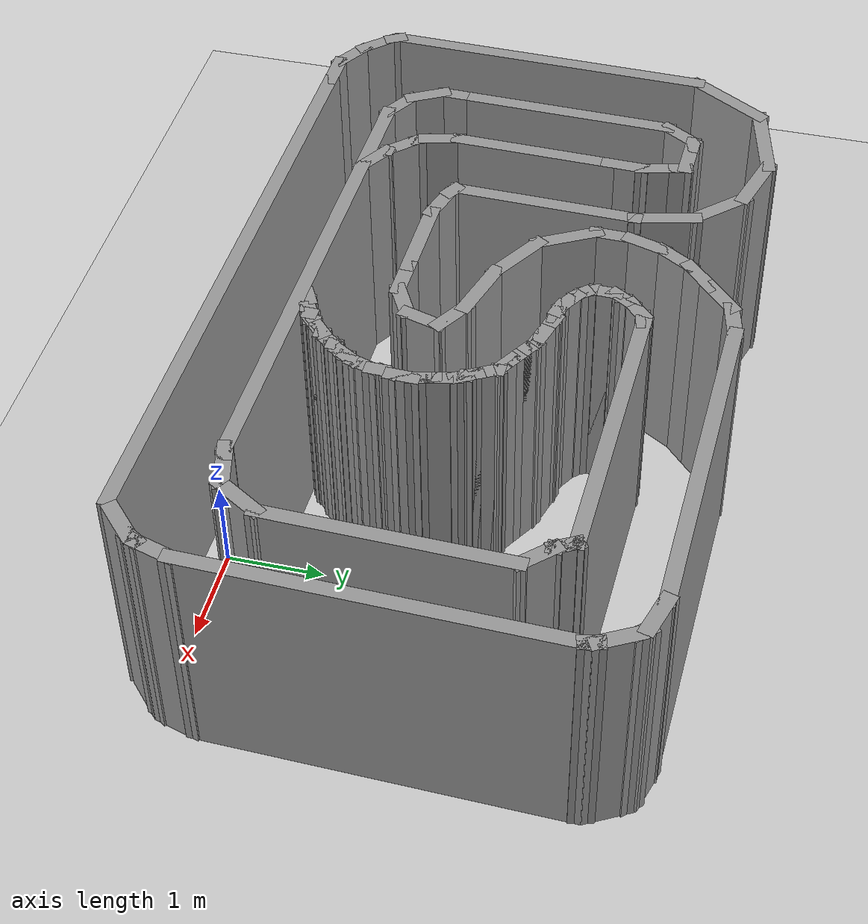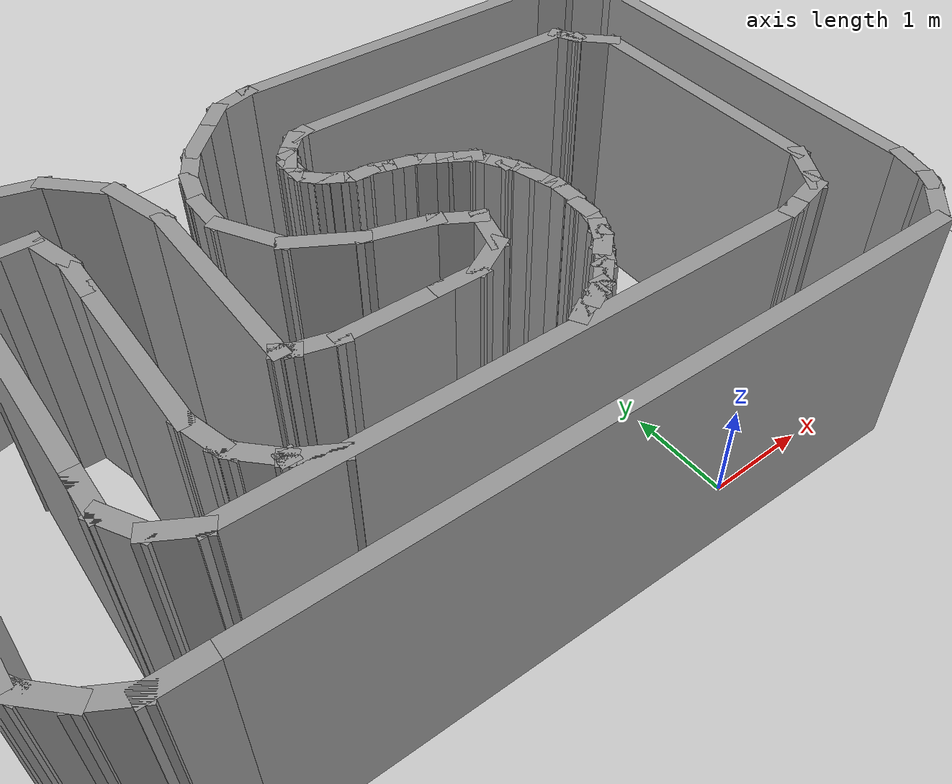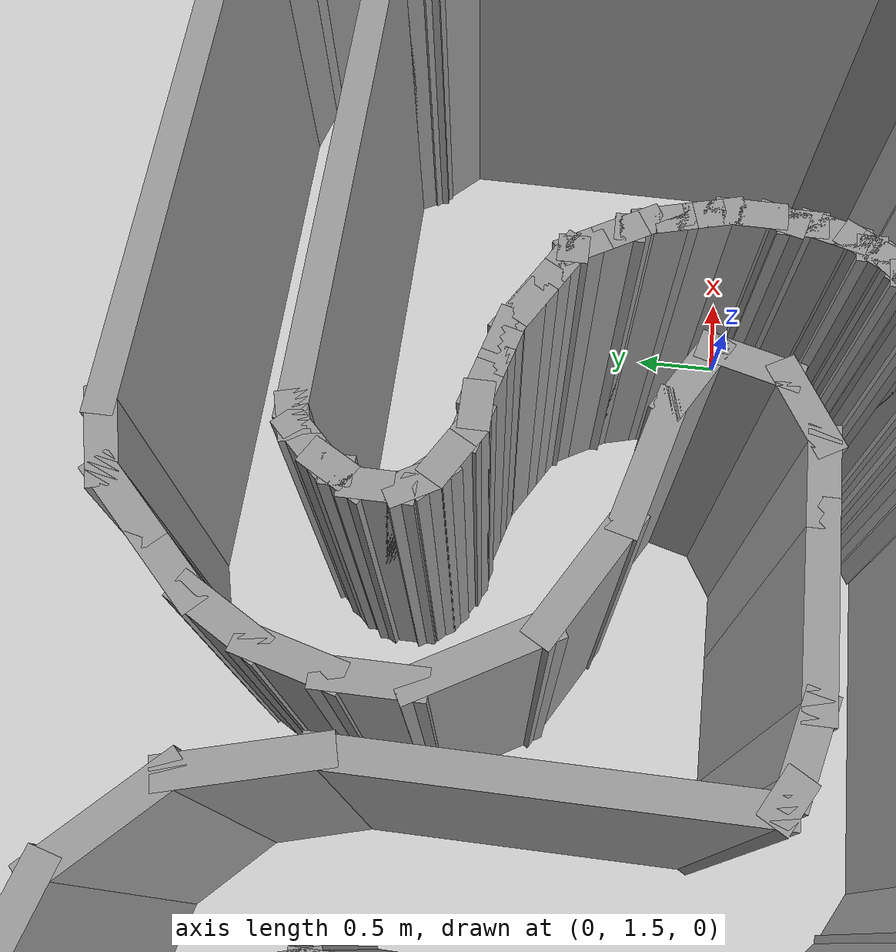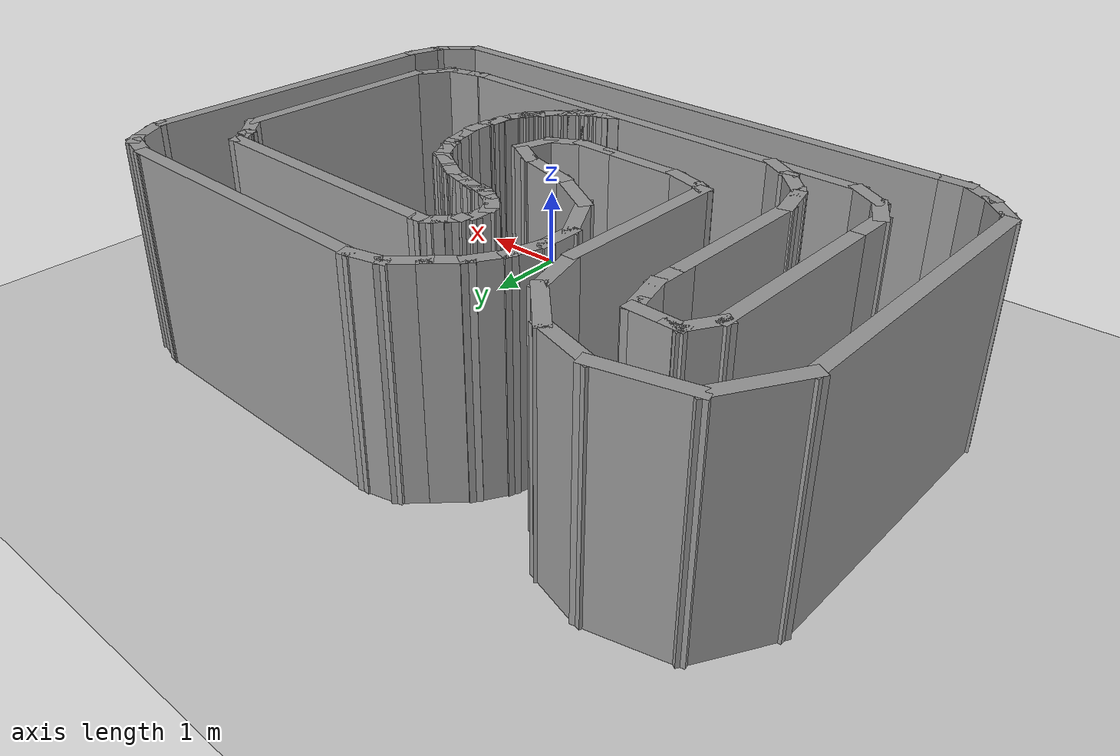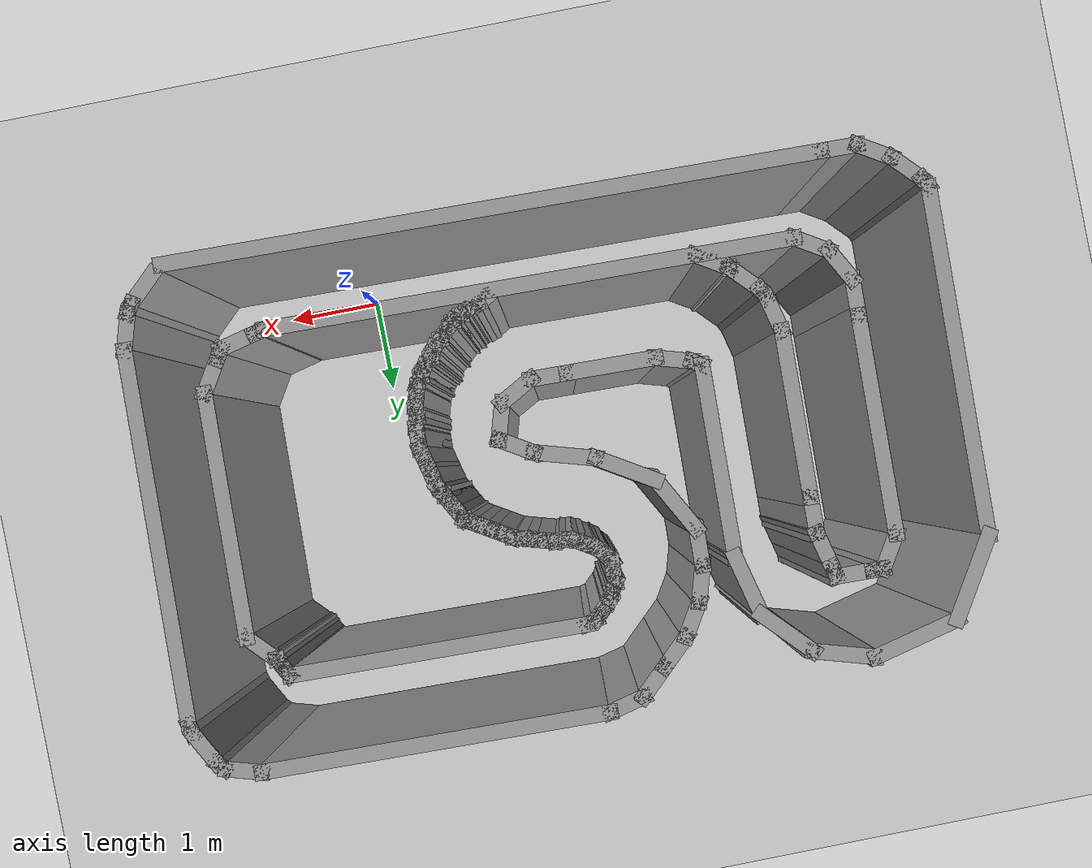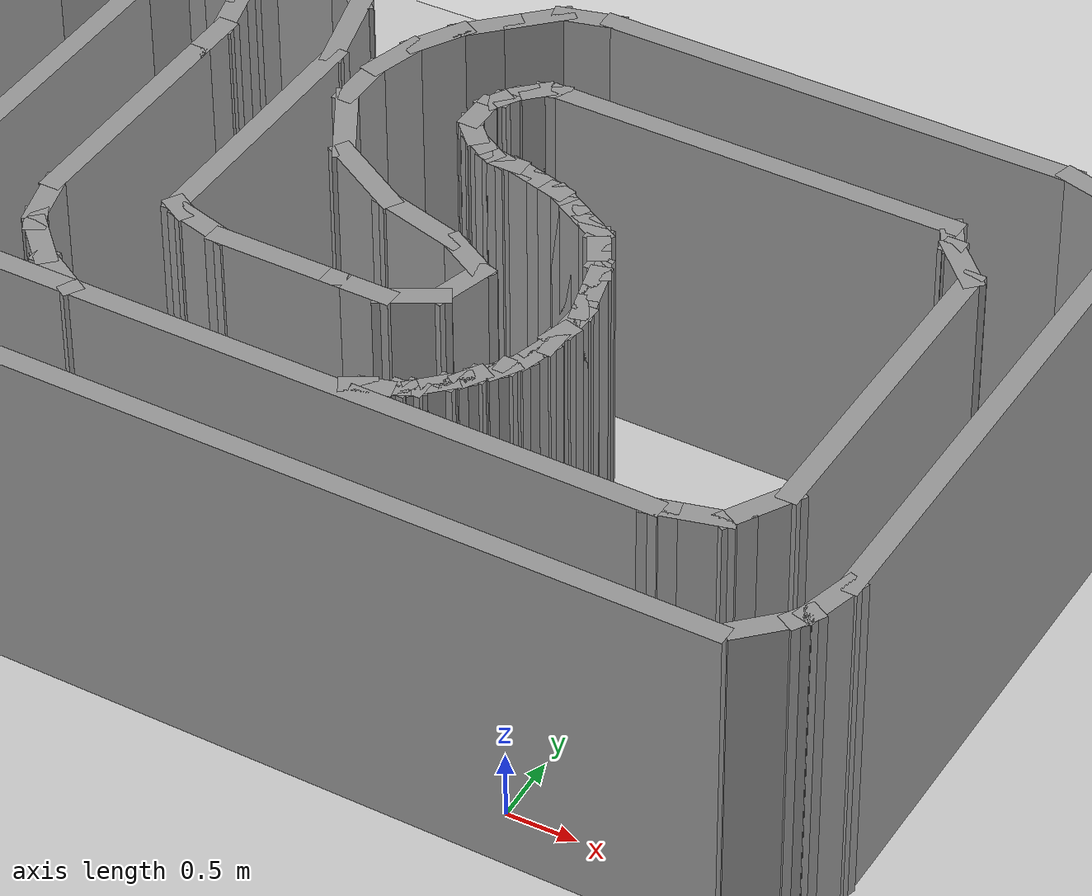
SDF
<sdf version="1.7">
 <world name="default">
  <light name="sun" type="directional">
   <pose>0 0 10 0 -0 0</pose>
   <diffuse>0.8 0.8 0.8 1</diffuse>
   <specular>0.2 0.2 0.2 1</specular>
   <attenuation>
    <range>1000</range>
    <constant>0.9</constant>
    <linear>0.01</linear>
    <quadratic>0.001</quadratic>
   </attenuation>
   <direction>-0.5 0.1 -0.9</direction>
   <spot><inner_angle>0</inner_angle><outer_angle>0</outer_angle><falloff>0</falloff></spot>
  </light>
  <model name="ground_plane">
   <static>1</static>
   <link name="link">
    <collision name="collision">
     <geometry><plane><normal>0 0 1</normal><size>100 100</size></plane></geometry>
     <surface>
      <contact><collide_bitmask>65535</collide_bitmask></contact>
      <friction><ode><mu>100</mu><mu2>50</mu2></ode></friction>
     </surface>
    </collision>
    <visual name="visual">
     <cast_shadows>0</cast_shadows>
     <geometry><plane><normal>0 0 1</normal><size>100 100</size></plane></geometry>
     <material>
      <script><uri>file://media/materials/scripts/gazebo.material</uri><name>Gazebo/Grey</name></script>
     </material>
    </visual>
   </link>
  </model>
  <gravity>0 0 -9.8</gravity>
  <magnetic_field>6e-06 2.3e-05 -4.2e-05</magnetic_field>
  <atmosphere type="adiabatic"/>
  <physics type="ode">
   <max_step_size>0.001</max_step_size>
   <real_time_factor>1</real_time_factor>
   <real_time_update_rate>1000</real_time_update_rate>
  </physics>
  <scene><ambient>0.4 0.4 0.4 1</ambient><background>0.7 0.7 0.7 1</background><shadows>1</shadows></scene>
  <spherical_coordinates>
   <surface_model>EARTH_WGS84</surface_model>
   <latitude_deg>0</latitude_deg>
   <longitude_deg>0</longitude_deg>
   <elevation>0</elevation>
   <heading_deg>0</heading_deg>
  </spherical_coordinates>
  <model name="t11">
   <pose>-1.75336 2.18774 -0 0 -0 1.54563</pose>
   <link name="Wall_10">
    <collision name="Wall_10_Collision">
     <geometry><box><size>1 0.15 2.5</size></box></geometry>
     <pose>0 0 1.25 0 -0 0</pose>
    </collision>
    <visual name="Wall_10_Visual">
     <pose>0 0 1.25 0 -0 0</pose>
     <geometry><box><size>1 0.15 2.5</size></box></geometry>
     <material>
      <script><uri>file://media/materials/scripts/gazebo.material</uri><name>Gazebo/Grey</name></script>
      <ambient>1 1 1 1</ambient>
     </material>
     <meta><layer>0</layer></meta>
    </visual>
    <pose>-0.781809 0.629649 0 0 -0 -1.5708</pose>
   </link>
   <link name="Wall_100">
    <collision name="Wall_100_Collision">
     <geometry><box><size>0.25 0.15 2.5</size></box></geometry>
     <pose>0 0 1.25 0 -0 0</pose>
    </collision>
    <visual name="Wall_100_Visual">
     <pose>0 0 1.25 0 -0 0</pose>
     <geometry><box><size>0.25 0.15 2.5</size></box></geometry>
     <material>
      <script><uri>file://media/materials/scripts/gazebo.material</uri><name>Gazebo/Grey</name></script>
      <ambient>1 1 1 1</ambient>
     </material>
     <meta><layer>0</layer></meta>
    </visual>
    <pose>0.204905 -1.11458 0 0 -0 -2.61799</pose>
   </link>
   <link name="Wall_101">
    <collision name="Wall_101_Collision">
     <geometry><box><size>0.15 0.15 2.5</size></box></geometry>
     <pose>0 0 1.25 0 -0 0</pose>
    </collision>
    <visual name="Wall_101_Visual">
     <pose>0 0 1.25 0 -0 0</pose>
     <geometry><box><size>0.15 0.15 2.5</size></box></geometry>
     <material>
      <script><uri>file://media/materials/scripts/gazebo.material</uri><name>Gazebo/Grey</name></script>
      <ambient>1 1 1 1</ambient>
     </material>
     <meta><layer>0</layer></meta>
    </visual>
    <pose>0.161604 -1.13958 0 0 -0 0</pose>
   </link>
   <link name="Wall_102">
    <collision name="Wall_102_Collision">
     <geometry><box><size>0.25 0.15 2.5</size></box></geometry>
     <pose>0 0 1.25 0 -0 0</pose>
    </collision>
    <visual name="Wall_102_Visual">
     <pose>0 0 1.25 0 -0 0</pose>
     <geometry><box><size>0.25 0.15 2.5</size></box></geometry>
     <material>
      <script><uri>file://media/materials/scripts/gazebo.material</uri><name>Gazebo/Grey</name></script>
      <ambient>1 1 1 1</ambient>
     </material>
     <meta><layer>0</layer></meta>
    </visual>
    <pose>0.118303 -1.16458 0 0 -0 -2.61799</pose>
   </link>
   <link name="Wall_103">
    <collision name="Wall_103_Collision">
     <geometry><box><size>0.25 0.15 2.5</size></box></geometry>
     <pose>0 0 1.25 0 -0 0</pose>
    </collision>
    <visual name="Wall_103_Visual">
     <pose>0 0 1.25 0 -0 0</pose>
     <geometry><box><size>0.25 0.15 2.5</size></box></geometry>
     <material>
      <script><uri>file://media/materials/scripts/gazebo.material</uri><name>Gazebo/Grey</name></script>
      <ambient>1 1 1 1</ambient>
     </material>
     <meta><layer>0</layer></meta>
    </visual>
    <pose>0.026705 -1.20252 0 0 -0 -2.87979</pose>
   </link>
   <link name="Wall_104">
    <collision name="Wall_104_Collision">
     <geometry><box><size>0.25 0.15 2.5</size></box></geometry>
     <pose>0 0 1.25 0 -0 0</pose>
    </collision>
    <visual name="Wall_104_Visual">
     <pose>0 0 1.25 0 -0 0</pose>
     <geometry><box><size>0.25 0.15 2.5</size></box></geometry>
     <material>
      <script><uri>file://media/materials/scripts/gazebo.material</uri><name>Gazebo/Grey</name></script>
      <ambient>1 1 1 1</ambient>
     </material>
     <meta><layer>0</layer></meta>
    </visual>
    <pose>-0.069887 -1.22841 0 0 -0 -2.87979</pose>
   </link>
   <link name="Wall_105">
    <collision name="Wall_105_Collision">
     <geometry><box><size>0.25 0.15 2.5</size></box></geometry>
     <pose>0 0 1.25 0 -0 0</pose>
    </collision>
    <visual name="Wall_105_Visual">
     <pose>0 0 1.25 0 -0 0</pose>
     <geometry><box><size>0.25 0.15 2.5</size></box></geometry>
     <material>
      <script><uri>file://media/materials/scripts/gazebo.material</uri><name>Gazebo/Grey</name></script>
      <ambient>1 1 1 1</ambient>
     </material>
     <meta><layer>0</layer></meta>
    </visual>
    <pose>-0.16648 -1.25429 0 0 -0 -2.87979</pose>
   </link>
   <link name="Wall_106">
    <collision name="Wall_106_Collision">
     <geometry><box><size>0.25 0.15 2.5</size></box></geometry>
     <pose>0 0 1.25 0 -0 0</pose>
    </collision>
    <visual name="Wall_106_Visual">
     <pose>0 0 1.25 0 -0 0</pose>
     <geometry><box><size>0.25 0.15 2.5</size></box></geometry>
     <material>
      <script><uri>file://media/materials/scripts/gazebo.material</uri><name>Gazebo/Grey</name></script>
      <ambient>1 1 1 1</ambient>
     </material>
     <meta><layer>0</layer></meta>
    </visual>
    <pose>-0.263072 -1.28017 0 0 -0 -2.87979</pose>
   </link>
   <link name="Wall_107">
    <collision name="Wall_107_Collision">
     <geometry><box><size>0.25 0.15 2.5</size></box></geometry>
     <pose>0 0 1.25 0 -0 0</pose>
    </collision>
    <visual name="Wall_107_Visual">
     <pose>0 0 1.25 0 -0 0</pose>
     <geometry><box><size>0.25 0.15 2.5</size></box></geometry>
     <material>
      <script><uri>file://media/materials/scripts/gazebo.material</uri><name>Gazebo/Grey</name></script>
      <ambient>1 1 1 1</ambient>
     </material>
     <meta><layer>0</layer></meta>
    </visual>
    <pose>-0.361369 -1.29311 0 0 -0 3.14159</pose>
   </link>
   <link name="Wall_108">
    <collision name="Wall_108_Collision">
     <geometry><box><size>0.25 0.15 2.5</size></box></geometry>
     <pose>0 0 1.25 0 -0 0</pose>
    </collision>
    <visual name="Wall_108_Visual">
     <pose>0 0 1.25 0 -0 0</pose>
     <geometry><box><size>0.25 0.15 2.5</size></box></geometry>
     <material>
      <script><uri>file://media/materials/scripts/gazebo.material</uri><name>Gazebo/Grey</name></script>
      <ambient>1 1 1 1</ambient>
     </material>
     <meta><layer>0</layer></meta>
    </visual>
    <pose>-0.461369 -1.29311 0 0 -0 3.14159</pose>
   </link>
   <link name="Wall_109">
    <collision name="Wall_109_Collision">
     <geometry><box><size>0.25 0.15 2.5</size></box></geometry>
     <pose>0 0 1.25 0 -0 0</pose>
    </collision>
    <visual name="Wall_109_Visual">
     <pose>0 0 1.25 0 -0 0</pose>
     <geometry><box><size>0.25 0.15 2.5</size></box></geometry>
     <material>
      <script><uri>file://media/materials/scripts/gazebo.material</uri><name>Gazebo/Grey</name></script>
      <ambient>1 1 1 1</ambient>
     </material>
     <meta><layer>0</layer></meta>
    </visual>
    <pose>-0.559665 -1.28017 0 0 -0 2.87979</pose>
   </link>
   <link name="Wall_11">
    <collision name="Wall_11_Collision">
     <geometry><box><size>0.5 0.15 2.5</size></box></geometry>
     <pose>0 0 1.25 0 -0 0</pose>
    </collision>
    <visual name="Wall_11_Visual">
     <pose>0 0 1.25 0 -0 0</pose>
     <geometry><box><size>0.5 0.15 2.5</size></box></geometry>
     <material>
      <script><uri>file://media/materials/scripts/gazebo.material</uri><name>Gazebo/Grey</name></script>
      <ambient>1 1 1 1</ambient>
     </material>
     <meta><layer>0</layer></meta>
    </visual>
    <pose>-0.781809 0.029649 0 0 -0 -1.5708</pose>
   </link>
   <link name="Wall_110">
    <collision name="Wall_110_Collision">
     <geometry><box><size>0.25 0.15 2.5</size></box></geometry>
     <pose>0 0 1.25 0 -0 0</pose>
    </collision>
    <visual name="Wall_110_Visual">
     <pose>0 0 1.25 0 -0 0</pose>
     <geometry><box><size>0.25 0.15 2.5</size></box></geometry>
     <material>
      <script><uri>file://media/materials/scripts/gazebo.material</uri><name>Gazebo/Grey</name></script>
      <ambient>1 1 1 1</ambient>
     </material>
     <meta><layer>0</layer></meta>
    </visual>
    <pose>-0.657961 -1.26723 0 0 -0 3.14159</pose>
   </link>
   <link name="Wall_111">
    <collision name="Wall_111_Collision">
     <geometry><box><size>0.25 0.15 2.5</size></box></geometry>
     <pose>0 0 1.25 0 -0 0</pose>
    </collision>
    <visual name="Wall_111_Visual">
     <pose>0 0 1.25 0 -0 0</pose>
     <geometry><box><size>0.25 0.15 2.5</size></box></geometry>
     <material>
      <script><uri>file://media/materials/scripts/gazebo.material</uri><name>Gazebo/Grey</name></script>
      <ambient>1 1 1 1</ambient>
     </material>
     <meta><layer>0</layer></meta>
    </visual>
    <pose>-0.756258 -1.25429 0 0 -0 2.87979</pose>
   </link>
   <link name="Wall_112">
    <collision name="Wall_112_Collision">
     <geometry><box><size>0.25 0.15 2.5</size></box></geometry>
     <pose>0 0 1.25 0 -0 0</pose>
    </collision>
    <visual name="Wall_112_Visual">
     <pose>0 0 1.25 0 -0 0</pose>
     <geometry><box><size>0.25 0.15 2.5</size></box></geometry>
     <material>
      <script><uri>file://media/materials/scripts/gazebo.material</uri><name>Gazebo/Grey</name></script>
      <ambient>1 1 1 1</ambient>
     </material>
     <meta><layer>0</layer></meta>
    </visual>
    <pose>-0.85285 -1.22841 0 0 -0 2.87979</pose>
   </link>
   <link name="Wall_113">
    <collision name="Wall_113_Collision">
     <geometry><box><size>0.25 0.15 2.5</size></box></geometry>
     <pose>0 0 1.25 0 -0 0</pose>
    </collision>
    <visual name="Wall_113_Visual">
     <pose>0 0 1.25 0 -0 0</pose>
     <geometry><box><size>0.25 0.15 2.5</size></box></geometry>
     <material>
      <script><uri>file://media/materials/scripts/gazebo.material</uri><name>Gazebo/Grey</name></script>
      <ambient>1 1 1 1</ambient>
     </material>
     <meta><layer>0</layer></meta>
    </visual>
    <pose>-0.944448 -1.19047 0 0 -0 2.61799</pose>
   </link>
   <link name="Wall_114">
    <collision name="Wall_114_Collision">
     <geometry><box><size>0.15 0.15 2.5</size></box></geometry>
     <pose>0 0 1.25 0 -0 0</pose>
    </collision>
    <visual name="Wall_114_Visual">
     <pose>0 0 1.25 0 -0 0</pose>
     <geometry><box><size>0.15 0.15 2.5</size></box></geometry>
     <material>
      <script><uri>file://media/materials/scripts/gazebo.material</uri><name>Gazebo/Grey</name></script>
      <ambient>1 1 1 1</ambient>
     </material>
     <meta><layer>0</layer></meta>
    </visual>
    <pose>-0.987749 -1.16546 0 0 -0 0</pose>
   </link>
   <link name="Wall_115">
    <collision name="Wall_115_Collision">
     <geometry><box><size>0.25 0.15 2.5</size></box></geometry>
     <pose>0 0 1.25 0 -0 0</pose>
    </collision>
    <visual name="Wall_115_Visual">
     <pose>0 0 1.25 0 -0 0</pose>
     <geometry><box><size>0.25 0.15 2.5</size></box></geometry>
     <material>
      <script><uri>file://media/materials/scripts/gazebo.material</uri><name>Gazebo/Grey</name></script>
      <ambient>1 1 1 1</ambient>
     </material>
     <meta><layer>0</layer></meta>
    </visual>
    <pose>-1.03105 -1.14047 0 0 -0 2.61799</pose>
   </link>
   <link name="Wall_116">
    <collision name="Wall_116_Collision">
     <geometry><box><size>0.25 0.15 2.5</size></box></geometry>
     <pose>0 0 1.25 0 -0 0</pose>
    </collision>
    <visual name="Wall_116_Visual">
     <pose>0 0 1.25 0 -0 0</pose>
     <geometry><box><size>0.25 0.15 2.5</size></box></geometry>
     <material>
      <script><uri>file://media/materials/scripts/gazebo.material</uri><name>Gazebo/Grey</name></script>
      <ambient>1 1 1 1</ambient>
     </material>
     <meta><layer>0</layer></meta>
    </visual>
    <pose>-1.10971 -1.08011 0 0 -0 2.35619</pose>
   </link>
   <link name="Wall_117">
    <collision name="Wall_117_Collision">
     <geometry><box><size>0.15 0.15 2.5</size></box></geometry>
     <pose>0 0 1.25 0 -0 0</pose>
    </collision>
    <visual name="Wall_117_Visual">
     <pose>0 0 1.25 0 -0 0</pose>
     <geometry><box><size>0.15 0.15 2.5</size></box></geometry>
     <material>
      <script><uri>file://media/materials/scripts/gazebo.material</uri><name>Gazebo/Grey</name></script>
      <ambient>1 1 1 1</ambient>
     </material>
     <meta><layer>0</layer></meta>
    </visual>
    <pose>-1.14506 -1.04476 0 0 -0 0</pose>
   </link>
   <link name="Wall_118">
    <collision name="Wall_118_Collision">
     <geometry><box><size>0.15 0.15 2.5</size></box></geometry>
     <pose>0 0 1.25 0 -0 0</pose>
    </collision>
    <visual name="Wall_118_Visual">
     <pose>0 0 1.25 0 -0 0</pose>
     <geometry><box><size>0.15 0.15 2.5</size></box></geometry>
     <material>
      <script><uri>file://media/materials/scripts/gazebo.material</uri><name>Gazebo/Grey</name></script>
      <ambient>1 1 1 1</ambient>
     </material>
     <meta><layer>0</layer></meta>
    </visual>
    <pose>-1.14506 -1.04476 0 0 -0 0</pose>
   </link>
   <link name="Wall_119">
    <collision name="Wall_119_Collision">
     <geometry><box><size>0.25 0.15 2.5</size></box></geometry>
     <pose>0 0 1.25 0 -0 0</pose>
    </collision>
    <visual name="Wall_119_Visual">
     <pose>0 0 1.25 0 -0 0</pose>
     <geometry><box><size>0.25 0.15 2.5</size></box></geometry>
     <material>
      <script><uri>file://media/materials/scripts/gazebo.material</uri><name>Gazebo/Grey</name></script>
      <ambient>1 1 1 1</ambient>
     </material>
     <meta><layer>0</layer></meta>
    </visual>
    <pose>-1.18836 -1.01975 0 0 -0 2.61799</pose>
   </link>
   <link name="Wall_12">
    <collision name="Wall_12_Collision">
     <geometry><box><size>0.5 0.15 2.5</size></box></geometry>
     <pose>0 0 1.25 0 -0 0</pose>
    </collision>
    <visual name="Wall_12_Visual">
     <pose>0 0 1.25 0 -0 0</pose>
     <geometry><box><size>0.5 0.15 2.5</size></box></geometry>
     <material>
      <script><uri>file://media/materials/scripts/gazebo.material</uri><name>Gazebo/Grey</name></script>
      <ambient>1 1 1 1</ambient>
     </material>
     <meta><layer>0</layer></meta>
    </visual>
    <pose>-0.694309 -0.296906 0 0 -0 -1.0472</pose>
   </link>
   <link name="Wall_120">
    <collision name="Wall_120_Collision">
     <geometry><box><size>0.25 0.15 2.5</size></box></geometry>
     <pose>0 0 1.25 0 -0 0</pose>
    </collision>
    <visual name="Wall_120_Visual">
     <pose>0 0 1.25 0 -0 0</pose>
     <geometry><box><size>0.25 0.15 2.5</size></box></geometry>
     <material>
      <script><uri>file://media/materials/scripts/gazebo.material</uri><name>Gazebo/Grey</name></script>
      <ambient>1 1 1 1</ambient>
     </material>
     <meta><layer>0</layer></meta>
    </visual>
    <pose>-1.26702 -0.959399 0 0 -0 2.35619</pose>
   </link>
   <link name="Wall_121">
    <collision name="Wall_121_Collision">
     <geometry><box><size>0.15 0.15 2.5</size></box></geometry>
     <pose>0 0 1.25 0 -0 0</pose>
    </collision>
    <visual name="Wall_121_Visual">
     <pose>0 0 1.25 0 -0 0</pose>
     <geometry><box><size>0.15 0.15 2.5</size></box></geometry>
     <material>
      <script><uri>file://media/materials/scripts/gazebo.material</uri><name>Gazebo/Grey</name></script>
      <ambient>1 1 1 1</ambient>
     </material>
     <meta><layer>0</layer></meta>
    </visual>
    <pose>-1.30238 -0.924044 0 0 -0 0</pose>
   </link>
   <link name="Wall_122">
    <collision name="Wall_122_Collision">
     <geometry><box><size>0.25 0.15 2.5</size></box></geometry>
     <pose>0 0 1.25 0 -0 0</pose>
    </collision>
    <visual name="Wall_122_Visual">
     <pose>0 0 1.25 0 -0 0</pose>
     <geometry><box><size>0.25 0.15 2.5</size></box></geometry>
     <material>
      <script><uri>file://media/materials/scripts/gazebo.material</uri><name>Gazebo/Grey</name></script>
      <ambient>1 1 1 1</ambient>
     </material>
     <meta><layer>0</layer></meta>
    </visual>
    <pose>-1.33773 -0.888689 0 0 -0 2.35619</pose>
   </link>
   <link name="Wall_123">
    <collision name="Wall_123_Collision">
     <geometry><box><size>0.25 0.15 2.5</size></box></geometry>
     <pose>0 0 1.25 0 -0 0</pose>
    </collision>
    <visual name="Wall_123_Visual">
     <pose>0 0 1.25 0 -0 0</pose>
     <geometry><box><size>0.25 0.15 2.5</size></box></geometry>
     <material>
      <script><uri>file://media/materials/scripts/gazebo.material</uri><name>Gazebo/Grey</name></script>
      <ambient>1 1 1 1</ambient>
     </material>
     <meta><layer>0</layer></meta>
    </visual>
    <pose>-1.40844 -0.817978 0 0 -0 2.35619</pose>
   </link>
   <link name="Wall_124">
    <collision name="Wall_124_Collision">
     <geometry><box><size>0.15 0.15 2.5</size></box></geometry>
     <pose>0 0 1.25 0 -0 0</pose>
    </collision>
    <visual name="Wall_124_Visual">
     <pose>0 0 1.25 0 -0 0</pose>
     <geometry><box><size>0.15 0.15 2.5</size></box></geometry>
     <material>
      <script><uri>file://media/materials/scripts/gazebo.material</uri><name>Gazebo/Grey</name></script>
      <ambient>1 1 1 1</ambient>
     </material>
     <meta><layer>0</layer></meta>
    </visual>
    <pose>-1.4438 -0.782623 0 0 -0 0</pose>
   </link>
   <link name="Wall_125">
    <collision name="Wall_125_Collision">
     <geometry><box><size>0.25 0.15 2.5</size></box></geometry>
     <pose>0 0 1.25 0 -0 0</pose>
    </collision>
    <visual name="Wall_125_Visual">
     <pose>0 0 1.25 0 -0 0</pose>
     <geometry><box><size>0.25 0.15 2.5</size></box></geometry>
     <material>
      <script><uri>file://media/materials/scripts/gazebo.material</uri><name>Gazebo/Grey</name></script>
      <ambient>1 1 1 1</ambient>
     </material>
     <meta><layer>0</layer></meta>
    </visual>
    <pose>-1.4688 -0.739321 0 0 -0 2.0944</pose>
   </link>
   <link name="Wall_126">
    <collision name="Wall_126_Collision">
     <geometry><box><size>0.15 0.15 2.5</size></box></geometry>
     <pose>0 0 1.25 0 -0 0</pose>
    </collision>
    <visual name="Wall_126_Visual">
     <pose>0 0 1.25 0 -0 0</pose>
     <geometry><box><size>0.15 0.15 2.5</size></box></geometry>
     <material>
      <script><uri>file://media/materials/scripts/gazebo.material</uri><name>Gazebo/Grey</name></script>
      <ambient>1 1 1 1</ambient>
     </material>
     <meta><layer>0</layer></meta>
    </visual>
    <pose>-1.4938 -0.69602 0 0 -0 0</pose>
   </link>
   <link name="Wall_127">
    <collision name="Wall_127_Collision">
     <geometry><box><size>0.25 0.15 2.5</size></box></geometry>
     <pose>0 0 1.25 0 -0 0</pose>
    </collision>
    <visual name="Wall_127_Visual">
     <pose>0 0 1.25 0 -0 0</pose>
     <geometry><box><size>0.25 0.15 2.5</size></box></geometry>
     <material>
      <script><uri>file://media/materials/scripts/gazebo.material</uri><name>Gazebo/Grey</name></script>
      <ambient>1 1 1 1</ambient>
     </material>
     <meta><layer>0</layer></meta>
    </visual>
    <pose>-1.5188 -0.652719 0 0 -0 2.0944</pose>
   </link>
   <link name="Wall_128">
    <collision name="Wall_128_Collision">
     <geometry><box><size>0.25 0.15 2.5</size></box></geometry>
     <pose>0 0 1.25 0 -0 0</pose>
    </collision>
    <visual name="Wall_128_Visual">
     <pose>0 0 1.25 0 -0 0</pose>
     <geometry><box><size>0.25 0.15 2.5</size></box></geometry>
     <material>
      <script><uri>file://media/materials/scripts/gazebo.material</uri><name>Gazebo/Grey</name></script>
      <ambient>1 1 1 1</ambient>
     </material>
     <meta><layer>0</layer></meta>
    </visual>
    <pose>-1.55674 -0.561121 0 0 -0 1.8326</pose>
   </link>
   <link name="Wall_129">
    <collision name="Wall_129_Collision">
     <geometry><box><size>0.25 0.15 2.5</size></box></geometry>
     <pose>0 0 1.25 0 -0 0</pose>
    </collision>
    <visual name="Wall_129_Visual">
     <pose>0 0 1.25 0 -0 0</pose>
     <geometry><box><size>0.25 0.15 2.5</size></box></geometry>
     <material>
      <script><uri>file://media/materials/scripts/gazebo.material</uri><name>Gazebo/Grey</name></script>
      <ambient>1 1 1 1</ambient>
     </material>
     <meta><layer>0</layer></meta>
    </visual>
    <pose>-1.59468 -0.469524 0 0 -0 2.0944</pose>
   </link>
   <link name="Wall_13">
    <collision name="Wall_13_Collision">
     <geometry><box><size>0.5 0.15 2.5</size></box></geometry>
     <pose>0 0 1.25 0 -0 0</pose>
    </collision>
    <visual name="Wall_13_Visual">
     <pose>0 0 1.25 0 -0 0</pose>
     <geometry><box><size>0.5 0.15 2.5</size></box></geometry>
     <material>
      <script><uri>file://media/materials/scripts/gazebo.material</uri><name>Gazebo/Grey</name></script>
      <ambient>1 1 1 1</ambient>
     </material>
     <meta><layer>0</layer></meta>
    </visual>
    <pose>-0.437772 -0.493754 0 0 -0 -0.261799</pose>
   </link>
   <link name="Wall_14">
    <collision name="Wall_14_Collision">
     <geometry><box><size>0.5 0.15 2.5</size></box></geometry>
     <pose>0 0 1.25 0 -0 0</pose>
    </collision>
    <visual name="Wall_14_Visual">
     <pose>0 0 1.25 0 -0 0</pose>
     <geometry><box><size>0.5 0.15 2.5</size></box></geometry>
     <material>
      <script><uri>file://media/materials/scripts/gazebo.material</uri><name>Gazebo/Grey</name></script>
      <ambient>1 1 1 1</ambient>
     </material>
     <meta><layer>0</layer></meta>
    </visual>
    <pose>-0.181235 -0.387492 0 0 -0 1.0472</pose>
   </link>
   <link name="Wall_15">
    <collision name="Wall_15_Collision">
     <geometry><box><size>0.75 0.15 2.5</size></box></geometry>
     <pose>0 0 1.25 0 -0 0</pose>
    </collision>
    <visual name="Wall_15_Visual">
     <pose>0 0 1.25 0 -0 0</pose>
     <geometry><box><size>0.75 0.15 2.5</size></box></geometry>
     <material>
      <script><uri>file://media/materials/scripts/gazebo.material</uri><name>Gazebo/Grey</name></script>
      <ambient>1 1 1 1</ambient>
     </material>
     <meta><layer>0</layer></meta>
    </visual>
    <pose>-0.01609 0.05384 0 0 -0 1.309</pose>
   </link>
   <link name="Wall_16">
    <collision name="Wall_16_Collision">
     <geometry><box><size>0.75 0.15 2.5</size></box></geometry>
     <pose>0 0 1.25 0 -0 0</pose>
    </collision>
    <visual name="Wall_16_Visual">
     <pose>0 0 1.25 0 -0 0</pose>
     <geometry><box><size>0.75 0.15 2.5</size></box></geometry>
     <material>
      <script><uri>file://media/materials/scripts/gazebo.material</uri><name>Gazebo/Grey</name></script>
      <ambient>1 1 1 1</ambient>
     </material>
     <meta><layer>0</layer></meta>
    </visual>
    <pose>0.211556 0.603425 0 0 -0 1.0472</pose>
   </link>
   <link name="Wall_17">
    <collision name="Wall_17_Collision">
     <geometry><box><size>0.75 0.15 2.5</size></box></geometry>
     <pose>0 0 1.25 0 -0 0</pose>
    </collision>
    <visual name="Wall_17_Visual">
     <pose>0 0 1.25 0 -0 0</pose>
     <geometry><box><size>0.75 0.15 2.5</size></box></geometry>
     <material>
      <script><uri>file://media/materials/scripts/gazebo.material</uri><name>Gazebo/Grey</name></script>
      <ambient>1 1 1 1</ambient>
     </material>
     <meta><layer>0</layer></meta>
    </visual>
    <pose>0.621364 1.01323 0 0 -0 0.523599</pose>
   </link>
   <link name="Wall_18">
    <collision name="Wall_18_Collision">
     <geometry><box><size>0.5 0.15 2.5</size></box></geometry>
     <pose>0 0 1.25 0 -0 0</pose>
    </collision>
    <visual name="Wall_18_Visual">
     <pose>0 0 1.25 0 -0 0</pose>
     <geometry><box><size>0.5 0.15 2.5</size></box></geometry>
     <material>
      <script><uri>file://media/materials/scripts/gazebo.material</uri><name>Gazebo/Grey</name></script>
      <ambient>1 1 1 1</ambient>
     </material>
     <meta><layer>0</layer></meta>
    </visual>
    <pose>1.05617 1.16323 0 0 -0 0</pose>
   </link>
   <link name="Wall_19">
    <collision name="Wall_19_Collision">
     <geometry><box><size>0.5 0.15 2.5</size></box></geometry>
     <pose>0 0 1.25 0 -0 0</pose>
    </collision>
    <visual name="Wall_19_Visual">
     <pose>0 0 1.25 0 -0 0</pose>
     <geometry><box><size>0.5 0.15 2.5</size></box></geometry>
     <material>
      <script><uri>file://media/materials/scripts/gazebo.material</uri><name>Gazebo/Grey</name></script>
      <ambient>1 1 1 1</ambient>
     </material>
     <meta><layer>0</layer></meta>
    </visual>
    <pose>1.40021 1.11794 0 0 -0 -0.261799</pose>
   </link>
   <link name="Wall_2">
    <collision name="Wall_2_Collision">
     <geometry><box><size>1 0.15 2.5</size></box></geometry>
     <pose>0 0 1.25 0 -0 0</pose>
    </collision>
    <visual name="Wall_2_Visual">
     <pose>0 0 1.25 0 -0 0</pose>
     <geometry><box><size>1 0.15 2.5</size></box></geometry>
     <material>
      <script><uri>file://media/materials/scripts/gazebo.material</uri><name>Gazebo/Grey</name></script>
      <ambient>1 1 1 1</ambient>
     </material>
     <meta><layer>0</layer></meta>
    </visual>
    <pose>1.77983 3.67197 0 0 -0 -0.523599</pose>
   </link>
   <link name="Wall_20">
    <collision name="Wall_20_Collision">
     <geometry><box><size>0.5 0.15 2.5</size></box></geometry>
     <pose>0 0 1.25 0 -0 0</pose>
    </collision>
    <visual name="Wall_20_Visual">
     <pose>0 0 1.25 0 -0 0</pose>
     <geometry><box><size>0.5 0.15 2.5</size></box></geometry>
     <material>
      <script><uri>file://media/materials/scripts/gazebo.material</uri><name>Gazebo/Grey</name></script>
      <ambient>1 1 1 1</ambient>
     </material>
     <meta><layer>0</layer></meta>
    </visual>
    <pose>1.7208 0.985146 0 0 -0 -0.523599</pose>
   </link>
   <link name="Wall_21">
    <collision name="Wall_21_Collision">
     <geometry><box><size>0.5 0.15 2.5</size></box></geometry>
     <pose>0 0 1.25 0 -0 0</pose>
    </collision>
    <visual name="Wall_21_Visual">
     <pose>0 0 1.25 0 -0 0</pose>
     <geometry><box><size>0.5 0.15 2.5</size></box></geometry>
     <material>
      <script><uri>file://media/materials/scripts/gazebo.material</uri><name>Gazebo/Grey</name></script>
      <ambient>1 1 1 1</ambient>
     </material>
     <meta><layer>0</layer></meta>
    </visual>
    <pose>1.9961 0.773902 0 0 -0 -0.785398</pose>
   </link>
   <link name="Wall_22">
    <collision name="Wall_22_Collision">
     <geometry><box><size>0.5 0.15 2.5</size></box></geometry>
     <pose>0 0 1.25 0 -0 0</pose>
    </collision>
    <visual name="Wall_22_Visual">
     <pose>0 0 1.25 0 -0 0</pose>
     <geometry><box><size>0.5 0.15 2.5</size></box></geometry>
     <material>
      <script><uri>file://media/materials/scripts/gazebo.material</uri><name>Gazebo/Grey</name></script>
      <ambient>1 1 1 1</ambient>
     </material>
     <meta><layer>0</layer></meta>
    </visual>
    <pose>2.24358 0.526415 0 0 -0 -0.785398</pose>
   </link>
   <link name="Wall_23">
    <collision name="Wall_23_Collision">
     <geometry><box><size>0.5 0.15 2.5</size></box></geometry>
     <pose>0 0 1.25 0 -0 0</pose>
    </collision>
    <visual name="Wall_23_Visual">
     <pose>0 0 1.25 0 -0 0</pose>
     <geometry><box><size>0.5 0.15 2.5</size></box></geometry>
     <material>
      <script><uri>file://media/materials/scripts/gazebo.material</uri><name>Gazebo/Grey</name></script>
      <ambient>1 1 1 1</ambient>
     </material>
     <meta><layer>0</layer></meta>
    </visual>
    <pose>2.41262 0.233634 0 0 -0 -1.309</pose>
   </link>
   <link name="Wall_24">
    <collision name="Wall_24_Collision">
     <geometry><box><size>3.5 0.15 2.5</size></box></geometry>
     <pose>0 0 1.25 0 -0 0</pose>
    </collision>
    <visual name="Wall_24_Visual">
     <pose>0 0 1.25 0 -0 0</pose>
     <geometry><box><size>3.5 0.15 2.5</size></box></geometry>
     <material>
      <script><uri>file://media/materials/scripts/gazebo.material</uri><name>Gazebo/Grey</name></script>
      <ambient>1 1 1 1</ambient>
     </material>
     <meta><layer>0</layer></meta>
    </visual>
    <pose>2.45792 -1.6104 0 0 -0 -1.5708</pose>
   </link>
   <link name="Wall_25">
    <collision name="Wall_25_Collision">
     <geometry><box><size>0.5 0.15 2.5</size></box></geometry>
     <pose>0 0 1.25 0 -0 0</pose>
    </collision>
    <visual name="Wall_25_Visual">
     <pose>0 0 1.25 0 -0 0</pose>
     <geometry><box><size>0.5 0.15 2.5</size></box></geometry>
     <material>
      <script><uri>file://media/materials/scripts/gazebo.material</uri><name>Gazebo/Grey</name></script>
      <ambient>1 1 1 1</ambient>
     </material>
     <meta><layer>0</layer></meta>
    </visual>
    <pose>2.41262 -3.45444 0 0 -0 -1.8326</pose>
   </link>
   <link name="Wall_26">
    <collision name="Wall_26_Collision">
     <geometry><box><size>0.25 0.15 2.5</size></box></geometry>
     <pose>0 0 1.25 0 -0 0</pose>
    </collision>
    <visual name="Wall_26_Visual">
     <pose>0 0 1.25 0 -0 0</pose>
     <geometry><box><size>0.25 0.15 2.5</size></box></geometry>
     <material>
      <script><uri>file://media/materials/scripts/gazebo.material</uri><name>Gazebo/Grey</name></script>
      <ambient>1 1 1 1</ambient>
     </material>
     <meta><layer>0</layer></meta>
    </visual>
    <pose>2.33197 -3.65883 0 0 -0 -2.35619</pose>
   </link>
   <link name="Wall_27">
    <collision name="Wall_27_Collision">
     <geometry><box><size>0.5 0.15 2.5</size></box></geometry>
     <pose>0 0 1.25 0 -0 0</pose>
    </collision>
    <visual name="Wall_27_Visual">
     <pose>0 0 1.25 0 -0 0</pose>
     <geometry><box><size>0.5 0.15 2.5</size></box></geometry>
     <material>
      <script><uri>file://media/materials/scripts/gazebo.material</uri><name>Gazebo/Grey</name></script>
      <ambient>1 1 1 1</ambient>
     </material>
     <meta><layer>0</layer></meta>
    </visual>
    <pose>2.14506 -3.78169 0 0 -0 -2.61799</pose>
   </link>
   <link name="Wall_28">
    <collision name="Wall_28_Collision">
     <geometry><box><size>0.25 0.15 2.5</size></box></geometry>
     <pose>0 0 1.25 0 -0 0</pose>
    </collision>
    <visual name="Wall_28_Visual">
     <pose>0 0 1.25 0 -0 0</pose>
     <geometry><box><size>0.25 0.15 2.5</size></box></geometry>
     <material>
      <script><uri>file://media/materials/scripts/gazebo.material</uri><name>Gazebo/Grey</name></script>
      <ambient>1 1 1 1</ambient>
     </material>
     <meta><layer>0</layer></meta>
    </visual>
    <pose>1.94521 -3.88213 0 0 -0 -2.87979</pose>
   </link>
   <link name="Wall_29">
    <collision name="Wall_29_Collision">
     <geometry><box><size>3.75 0.15 2.5</size></box></geometry>
     <pose>0 0 1.25 0 -0 0</pose>
    </collision>
    <visual name="Wall_29_Visual">
     <pose>0 0 1.25 0 -0 0</pose>
     <geometry><box><size>3.75 0.15 2.5</size></box></geometry>
     <material>
      <script><uri>file://media/materials/scripts/gazebo.material</uri><name>Gazebo/Grey</name></script>
      <ambient>1 1 1 1</ambient>
     </material>
     <meta><layer>0</layer></meta>
    </visual>
    <pose>0.096917 -3.89507 0 0 -0 3.14159</pose>
   </link>
   <link name="Wall_3">
    <collision name="Wall_3_Collision">
     <geometry><box><size>1 0.15 2.5</size></box></geometry>
     <pose>0 0 1.25 0 -0 0</pose>
    </collision>
    <visual name="Wall_3_Visual">
     <pose>0 0 1.25 0 -0 0</pose>
     <geometry><box><size>1 0.15 2.5</size></box></geometry>
     <material>
      <script><uri>file://media/materials/scripts/gazebo.material</uri><name>Gazebo/Grey</name></script>
      <ambient>1 1 1 1</ambient>
     </material>
     <meta><layer>0</layer></meta>
    </visual>
    <pose>2.25789 3.04895 0 0 -0 -1.309</pose>
   </link>
   <link name="Wall_30">
    <collision name="Wall_30_Collision">
     <geometry><box><size>0.5 0.15 2.5</size></box></geometry>
     <pose>0 0 1.25 0 -0 0</pose>
    </collision>
    <visual name="Wall_30_Visual">
     <pose>0 0 1.25 0 -0 0</pose>
     <geometry><box><size>0.5 0.15 2.5</size></box></geometry>
     <material>
      <script><uri>file://media/materials/scripts/gazebo.material</uri><name>Gazebo/Grey</name></script>
      <ambient>1 1 1 1</ambient>
     </material>
     <meta><layer>0</layer></meta>
    </visual>
    <pose>-1.87212 -3.84978 0 0 -0 2.87979</pose>
   </link>
   <link name="Wall_31">
    <collision name="Wall_31_Collision">
     <geometry><box><size>0.25 0.15 2.5</size></box></geometry>
     <pose>0 0 1.25 0 -0 0</pose>
    </collision>
    <visual name="Wall_31_Visual">
     <pose>0 0 1.25 0 -0 0</pose>
     <geometry><box><size>0.25 0.15 2.5</size></box></geometry>
     <material>
      <script><uri>file://media/materials/scripts/gazebo.material</uri><name>Gazebo/Grey</name></script>
      <ambient>1 1 1 1</ambient>
     </material>
     <meta><layer>0</layer></meta>
    </visual>
    <pose>-2.08446 -3.77948 0 0 -0 2.61799</pose>
   </link>
   <link name="Wall_32">
    <collision name="Wall_32_Collision">
     <geometry><box><size>0.5 0.15 2.5</size></box></geometry>
     <pose>0 0 1.25 0 -0 0</pose>
    </collision>
    <visual name="Wall_32_Visual">
     <pose>0 0 1.25 0 -0 0</pose>
     <geometry><box><size>0.5 0.15 2.5</size></box></geometry>
     <material>
      <script><uri>file://media/materials/scripts/gazebo.material</uri><name>Gazebo/Grey</name></script>
      <ambient>1 1 1 1</ambient>
     </material>
     <meta><layer>0</layer></meta>
    </visual>
    <pose>-2.2515 -3.63074 0 0 -0 2.35619</pose>
   </link>
   <link name="Wall_34">
    <collision name="Wall_34_Collision">
     <geometry><box><size>3.5 0.15 2.5</size></box></geometry>
     <pose>0 0 1.25 0 -0 0</pose>
    </collision>
    <visual name="Wall_34_Visual">
     <pose>0 0 1.25 0 -0 0</pose>
     <geometry><box><size>3.5 0.15 2.5</size></box></geometry>
     <material>
      <script><uri>file://media/materials/scripts/gazebo.material</uri><name>Gazebo/Grey</name></script>
      <ambient>1 1 1 1</ambient>
     </material>
     <meta><layer>0</layer></meta>
    </visual>
    <pose>-0.26323 3.88447 0 0 -0 3.14159</pose>
   </link>
   <link name="Wall_35">
    <collision name="Wall_35_Collision">
     <geometry><box><size>0.25 0.15 2.5</size></box></geometry>
     <pose>0 0 1.25 0 -0 0</pose>
    </collision>
    <visual name="Wall_35_Visual">
     <pose>0 0 1.25 0 -0 0</pose>
     <geometry><box><size>0.25 0.15 2.5</size></box></geometry>
     <material>
      <script><uri>file://media/materials/scripts/gazebo.material</uri><name>Gazebo/Grey</name></script>
      <ambient>1 1 1 1</ambient>
     </material>
     <meta><layer>0</layer></meta>
    </visual>
    <pose>-1.98153 3.85947 0 0 -0 -2.61799</pose>
   </link>
   <link name="Wall_36">
    <collision name="Wall_36_Collision">
     <geometry><box><size>0.5 0.15 2.5</size></box></geometry>
     <pose>0 0 1.25 0 -0 0</pose>
    </collision>
    <visual name="Wall_36_Visual">
     <pose>0 0 1.25 0 -0 0</pose>
     <geometry><box><size>0.5 0.15 2.5</size></box></geometry>
     <material>
      <script><uri>file://media/materials/scripts/gazebo.material</uri><name>Gazebo/Grey</name></script>
      <ambient>1 1 1 1</ambient>
     </material>
     <meta><layer>0</layer></meta>
    </visual>
    <pose>-2.14858 3.71073 0 0 -0 -2.35619</pose>
   </link>
   <link name="Wall_37">
    <collision name="Wall_37_Collision">
     <geometry><box><size>0.5 0.15 2.5</size></box></geometry>
     <pose>0 0 1.25 0 -0 0</pose>
    </collision>
    <visual name="Wall_37_Visual">
     <pose>0 0 1.25 0 -0 0</pose>
     <geometry><box><size>0.5 0.15 2.5</size></box></geometry>
     <material>
      <script><uri>file://media/materials/scripts/gazebo.material</uri><name>Gazebo/Grey</name></script>
      <ambient>1 1 1 1</ambient>
     </material>
     <meta><layer>0</layer></meta>
    </visual>
    <pose>-2.35982 3.43543 0 0 -0 -2.0944</pose>
   </link>
   <link name="Wall_38">
    <collision name="Wall_38_Collision">
     <geometry><box><size>0.5 0.15 2.5</size></box></geometry>
     <pose>0 0 1.25 0 -0 0</pose>
    </collision>
    <visual name="Wall_38_Visual">
     <pose>0 0 1.25 0 -0 0</pose>
     <geometry><box><size>0.5 0.15 2.5</size></box></geometry>
     <material>
      <script><uri>file://media/materials/scripts/gazebo.material</uri><name>Gazebo/Grey</name></script>
      <ambient>1 1 1 1</ambient>
     </material>
     <meta><layer>0</layer></meta>
    </visual>
    <pose>-2.44732 3.10888 0 0 -0 -1.5708</pose>
   </link>
   <link name="Wall_39">
    <collision name="Wall_39_Collision">
     <geometry><box><size>6.5 0.15 2.5</size></box></geometry>
     <pose>0 0 1.25 0 -0 0</pose>
    </collision>
    <visual name="Wall_39_Visual">
     <pose>0 0 1.25 0 -0 0</pose>
     <geometry><box><size>6.5 0.15 2.5</size></box></geometry>
     <material>
      <script><uri>file://media/materials/scripts/gazebo.material</uri><name>Gazebo/Grey</name></script>
      <ambient>1 1 1 1</ambient>
     </material>
     <meta><layer>0</layer></meta>
    </visual>
    <pose>-2.44732 -0.241123 0 0 -0 -1.5708</pose>
   </link>
   <link name="Wall_4">
    <collision name="Wall_4_Collision">
     <geometry><box><size>0.75 0.15 2.5</size></box></geometry>
     <pose>0 0 1.25 0 -0 0</pose>
    </collision>
    <visual name="Wall_4_Visual">
     <pose>0 0 1.25 0 -0 0</pose>
     <geometry><box><size>0.75 0.15 2.5</size></box></geometry>
     <material>
      <script><uri>file://media/materials/scripts/gazebo.material</uri><name>Gazebo/Grey</name></script>
      <ambient>1 1 1 1</ambient>
     </material>
     <meta><layer>0</layer></meta>
    </visual>
    <pose>2.29024 2.34866 0 0 -0 -1.8326</pose>
   </link>
   <link name="Wall_41">
    <collision name="Wall_41_Collision">
     <geometry><box><size>5.25 0.15 2.5</size></box></geometry>
     <pose>0 0 1.25 0 -0 0</pose>
    </collision>
    <visual name="Wall_41_Visual">
     <pose>0 0 1.25 0 -0 0</pose>
     <geometry><box><size>5.25 0.15 2.5</size></box></geometry>
     <material>
      <script><uri>file://media/materials/scripts/gazebo.material</uri><name>Gazebo/Grey</name></script>
      <ambient>1 1 1 1</ambient>
     </material>
     <meta><layer>0</layer></meta>
    </visual>
    <pose>-1.67823 -0.005527 0 0 -0 1.5708</pose>
   </link>
   <link name="Wall_42">
    <collision name="Wall_42_Collision">
     <geometry><box><size>0.5 0.15 2.5</size></box></geometry>
     <pose>0 0 1.25 0 -0 0</pose>
    </collision>
    <visual name="Wall_42_Visual">
     <pose>0 0 1.25 0 -0 0</pose>
     <geometry><box><size>0.5 0.15 2.5</size></box></geometry>
     <material>
      <script><uri>file://media/materials/scripts/gazebo.material</uri><name>Gazebo/Grey</name></script>
      <ambient>1 1 1 1</ambient>
     </material>
     <meta><layer>0</layer></meta>
    </visual>
    <pose>-1.59073 2.69603 0 0 -0 1.0472</pose>
   </link>
   <link name="Wall_43">
    <collision name="Wall_43_Collision">
     <geometry><box><size>0.5 0.15 2.5</size></box></geometry>
     <pose>0 0 1.25 0 -0 0</pose>
    </collision>
    <visual name="Wall_43_Visual">
     <pose>0 0 1.25 0 -0 0</pose>
     <geometry><box><size>0.5 0.15 2.5</size></box></geometry>
     <material>
      <script><uri>file://media/materials/scripts/gazebo.material</uri><name>Gazebo/Grey</name></script>
      <ambient>1 1 1 1</ambient>
     </material>
     <meta><layer>0</layer></meta>
    </visual>
    <pose>-1.35167 2.93508 0 0 -0 0.523599</pose>
   </link>
   <link name="Wall_44">
    <collision name="Wall_44_Collision">
     <geometry><box><size>0.5 0.15 2.5</size></box></geometry>
     <pose>0 0 1.25 0 -0 0</pose>
    </collision>
    <visual name="Wall_44_Visual">
     <pose>0 0 1.25 0 -0 0</pose>
     <geometry><box><size>0.5 0.15 2.5</size></box></geometry>
     <material>
      <script><uri>file://media/materials/scripts/gazebo.material</uri><name>Gazebo/Grey</name></script>
      <ambient>1 1 1 1</ambient>
     </material>
     <meta><layer>0</layer></meta>
    </visual>
    <pose>-1.02512 3.02258 0 0 -0 0</pose>
   </link>
   <link name="Wall_45">
    <collision name="Wall_45_Collision">
     <geometry><box><size>2.25 0.15 2.5</size></box></geometry>
     <pose>0 0 1.25 0 -0 0</pose>
    </collision>
    <visual name="Wall_45_Visual">
     <pose>0 0 1.25 0 -0 0</pose>
     <geometry><box><size>2.25 0.15 2.5</size></box></geometry>
     <material>
      <script><uri>file://media/materials/scripts/gazebo.material</uri><name>Gazebo/Grey</name></script>
      <ambient>1 1 1 1</ambient>
     </material>
     <meta><layer>0</layer></meta>
    </visual>
    <pose>0.199879 3.02258 0 0 -0 0</pose>
   </link>
   <link name="Wall_46">
    <collision name="Wall_46_Collision">
     <geometry><box><size>0.5 0.15 2.5</size></box></geometry>
     <pose>0 0 1.25 0 -0 0</pose>
    </collision>
    <visual name="Wall_46_Visual">
     <pose>0 0 1.25 0 -0 0</pose>
     <geometry><box><size>0.5 0.15 2.5</size></box></geometry>
     <material>
      <script><uri>file://media/materials/scripts/gazebo.material</uri><name>Gazebo/Grey</name></script>
      <ambient>1 1 1 1</ambient>
     </material>
     <meta><layer>0</layer></meta>
    </visual>
    <pose>1.40143 2.93508 0 0 -0 -0.523599</pose>
   </link>
   <link name="Wall_47">
    <collision name="Wall_47_Collision">
     <geometry><box><size>0.25 0.15 2.5</size></box></geometry>
     <pose>0 0 1.25 0 -0 0</pose>
    </collision>
    <visual name="Wall_47_Visual">
     <pose>0 0 1.25 0 -0 0</pose>
     <geometry><box><size>0.25 0.15 2.5</size></box></geometry>
     <material>
      <script><uri>file://media/materials/scripts/gazebo.material</uri><name>Gazebo/Grey</name></script>
      <ambient>1 1 1 1</ambient>
     </material>
     <meta><layer>0</layer></meta>
    </visual>
    <pose>1.55299 2.79758 0 0 -0 -1.5708</pose>
   </link>
   <link name="Wall_48">
    <collision name="Wall_48_Collision">
     <geometry><box><size>0.5 0.15 2.5</size></box></geometry>
     <pose>0 0 1.25 0 -0 0</pose>
    </collision>
    <visual name="Wall_48_Visual">
     <pose>0 0 1.25 0 -0 0</pose>
     <geometry><box><size>0.5 0.15 2.5</size></box></geometry>
     <material>
      <script><uri>file://media/materials/scripts/gazebo.material</uri><name>Gazebo/Grey</name></script>
      <ambient>1 1 1 1</ambient>
     </material>
     <meta><layer>0</layer></meta>
    </visual>
    <pose>1.55299 2.57258 0 0 -0 -1.5708</pose>
   </link>
   <link name="Wall_49">
    <collision name="Wall_49_Collision">
     <geometry><box><size>0.25 0.15 2.5</size></box></geometry>
     <pose>0 0 1.25 0 -0 0</pose>
    </collision>
    <visual name="Wall_49_Visual">
     <pose>0 0 1.25 0 -0 0</pose>
     <geometry><box><size>0.25 0.15 2.5</size></box></geometry>
     <material>
      <script><uri>file://media/materials/scripts/gazebo.material</uri><name>Gazebo/Grey</name></script>
      <ambient>1 1 1 1</ambient>
     </material>
     <meta><layer>0</layer></meta>
    </visual>
    <pose>1.50469 2.38464 0 0 -0 -2.87979</pose>
   </link>
   <link name="Wall_5">
    <collision name="Wall_5_Collision">
     <geometry><box><size>0.75 0.15 2.5</size></box></geometry>
     <pose>0 0 1.25 0 -0 0</pose>
    </collision>
    <visual name="Wall_5_Visual">
     <pose>0 0 1.25 0 -0 0</pose>
     <geometry><box><size>0.75 0.15 2.5</size></box></geometry>
     <material>
      <script><uri>file://media/materials/scripts/gazebo.material</uri><name>Gazebo/Grey</name></script>
      <ambient>1 1 1 1</ambient>
     </material>
     <meta><layer>0</layer></meta>
    </visual>
    <pose>2.00047 1.84675 0 0 -0 -2.35619</pose>
   </link>
   <link name="Wall_50">
    <collision name="Wall_50_Collision">
     <geometry><box><size>0.5 0.15 2.5</size></box></geometry>
     <pose>0 0 1.25 0 -0 0</pose>
    </collision>
    <visual name="Wall_50_Visual">
     <pose>0 0 1.25 0 -0 0</pose>
     <geometry><box><size>0.5 0.15 2.5</size></box></geometry>
     <material>
      <script><uri>file://media/materials/scripts/gazebo.material</uri><name>Gazebo/Grey</name></script>
      <ambient>1 1 1 1</ambient>
     </material>
     <meta><layer>0</layer></meta>
    </visual>
    <pose>1.28736 2.32641 0 0 -0 -2.87979</pose>
   </link>
   <link name="Wall_51">
    <collision name="Wall_51_Collision">
     <geometry><box><size>0.5 0.15 2.5</size></box></geometry>
     <pose>0 0 1.25 0 -0 0</pose>
    </collision>
    <visual name="Wall_51_Visual">
     <pose>0 0 1.25 0 -0 0</pose>
     <geometry><box><size>0.5 0.15 2.5</size></box></geometry>
     <material>
      <script><uri>file://media/materials/scripts/gazebo.material</uri><name>Gazebo/Grey</name></script>
      <ambient>1 1 1 1</ambient>
     </material>
     <meta><layer>0</layer></meta>
    </visual>
    <pose>0.943322 2.28111 0 0 -0 3.14159</pose>
   </link>
   <link name="Wall_52">
    <collision name="Wall_52_Collision">
     <geometry><box><size>1.75 0.15 2.5</size></box></geometry>
     <pose>0 0 1.25 0 -0 0</pose>
    </collision>
    <visual name="Wall_52_Visual">
     <pose>0 0 1.25 0 -0 0</pose>
     <geometry><box><size>1.75 0.15 2.5</size></box></geometry>
     <material>
      <script><uri>file://media/materials/scripts/gazebo.material</uri><name>Gazebo/Grey</name></script>
      <ambient>1 1 1 1</ambient>
     </material>
     <meta><layer>0</layer></meta>
    </visual>
    <pose>-0.031678 2.28111 0 0 -0 3.14159</pose>
   </link>
   <link name="Wall_53">
    <collision name="Wall_53_Collision">
     <geometry><box><size>0.5 0.15 2.5</size></box></geometry>
     <pose>0 0 1.25 0 -0 0</pose>
    </collision>
    <visual name="Wall_53_Visual">
     <pose>0 0 1.25 0 -0 0</pose>
     <geometry><box><size>0.5 0.15 2.5</size></box></geometry>
     <material>
      <script><uri>file://media/materials/scripts/gazebo.material</uri><name>Gazebo/Grey</name></script>
      <ambient>1 1 1 1</ambient>
     </material>
     <meta><layer>0</layer></meta>
    </visual>
    <pose>-1.00072 2.23582 0 0 -0 -2.87979</pose>
   </link>
   <link name="Wall_54">
    <collision name="Wall_54_Collision">
     <geometry><box><size>0.25 0.15 2.5</size></box></geometry>
     <pose>0 0 1.25 0 -0 0</pose>
    </collision>
    <visual name="Wall_54_Visual">
     <pose>0 0 1.25 0 -0 0</pose>
     <geometry><box><size>0.25 0.15 2.5</size></box></geometry>
     <material>
      <script><uri>file://media/materials/scripts/gazebo.material</uri><name>Gazebo/Grey</name></script>
      <ambient>1 1 1 1</ambient>
     </material>
     <meta><layer>0</layer></meta>
    </visual>
    <pose>-1.21305 2.16553 0 0 -0 -2.61799</pose>
   </link>
   <link name="Wall_55">
    <collision name="Wall_55_Collision">
     <geometry><box><size>0.5 0.15 2.5</size></box></geometry>
     <pose>0 0 1.25 0 -0 0</pose>
    </collision>
    <visual name="Wall_55_Visual">
     <pose>0 0 1.25 0 -0 0</pose>
     <geometry><box><size>0.5 0.15 2.5</size></box></geometry>
     <material>
      <script><uri>file://media/materials/scripts/gazebo.material</uri><name>Gazebo/Grey</name></script>
      <ambient>1 1 1 1</ambient>
     </material>
     <meta><layer>0</layer></meta>
    </visual>
    <pose>-1.3801 2.01678 0 0 -0 -2.35619</pose>
   </link>
   <link name="Wall_56">
    <collision name="Wall_56_Collision">
     <geometry><box><size>0.15 0.15 2.5</size></box></geometry>
     <pose>0 0 1.25 0 -0 0</pose>
    </collision>
    <visual name="Wall_56_Visual">
     <pose>0 0 1.25 0 -0 0</pose>
     <geometry><box><size>0.15 0.15 2.5</size></box></geometry>
     <material>
      <script><uri>file://media/materials/scripts/gazebo.material</uri><name>Gazebo/Grey</name></script>
      <ambient>1 1 1 1</ambient>
     </material>
     <meta><layer>0</layer></meta>
    </visual>
    <pose>-1.50384 1.89304 0 0 -0 0</pose>
   </link>
   <link name="Wall_57">
    <collision name="Wall_57_Collision">
     <geometry><box><size>0.5 0.15 2.5</size></box></geometry>
     <pose>0 0 1.25 0 -0 0</pose>
    </collision>
    <visual name="Wall_57_Visual">
     <pose>0 0 1.25 0 -0 0</pose>
     <geometry><box><size>0.5 0.15 2.5</size></box></geometry>
     <material>
      <script><uri>file://media/materials/scripts/gazebo.material</uri><name>Gazebo/Grey</name></script>
      <ambient>1 1 1 1</ambient>
     </material>
     <meta><layer>0</layer></meta>
    </visual>
    <pose>-1.59134 1.74148 0 0 -0 -2.0944</pose>
   </link>
   <link name="Wall_59">
    <collision name="Wall_59_Collision">
     <geometry><box><size>0.25 0.15 2.5</size></box></geometry>
     <pose>0 0 1.25 0 -0 0</pose>
    </collision>
    <visual name="Wall_59_Visual">
     <pose>0 0 1.25 0 -0 0</pose>
     <geometry><box><size>0.25 0.15 2.5</size></box></geometry>
     <material>
      <script><uri>file://media/materials/scripts/gazebo.material</uri><name>Gazebo/Grey</name></script>
      <ambient>1 1 1 1</ambient>
     </material>
     <meta><layer>0</layer></meta>
    </visual>
    <pose>-1.66529 -2.60382 0 0 -0 -1.309</pose>
   </link>
   <link name="Wall_6">
    <collision name="Wall_6_Collision">
     <geometry><box><size>0.75 0.15 2.5</size></box></geometry>
     <pose>0 0 1.25 0 -0 0</pose>
    </collision>
    <visual name="Wall_6_Visual">
     <pose>0 0 1.25 0 -0 0</pose>
     <geometry><box><size>0.75 0.15 2.5</size></box></geometry>
     <material>
      <script><uri>file://media/materials/scripts/gazebo.material</uri><name>Gazebo/Grey</name></script>
      <ambient>1 1 1 1</ambient>
     </material>
     <meta><layer>0</layer></meta>
    </visual>
    <pose>1.49856 1.55697 0 0 -0 -2.87979</pose>
   </link>
   <link name="Wall_60">
    <collision name="Wall_60_Collision">
     <geometry><box><size>0.5 0.15 2.5</size></box></geometry>
     <pose>0 0 1.25 0 -0 0</pose>
    </collision>
    <visual name="Wall_60_Visual">
     <pose>0 0 1.25 0 -0 0</pose>
     <geometry><box><size>0.5 0.15 2.5</size></box></geometry>
     <material>
      <script><uri>file://media/materials/scripts/gazebo.material</uri><name>Gazebo/Grey</name></script>
      <ambient>1 1 1 1</ambient>
     </material>
     <meta><layer>0</layer></meta>
    </visual>
    <pose>-1.60705 -2.82116 0 0 -0 -1.309</pose>
   </link>
   <link name="Wall_61">
    <collision name="Wall_61_Collision">
     <geometry><box><size>0.25 0.15 2.5</size></box></geometry>
     <pose>0 0 1.25 0 -0 0</pose>
    </collision>
    <visual name="Wall_61_Visual">
     <pose>0 0 1.25 0 -0 0</pose>
     <geometry><box><size>0.25 0.15 2.5</size></box></geometry>
     <material>
      <script><uri>file://media/materials/scripts/gazebo.material</uri><name>Gazebo/Grey</name></script>
      <ambient>1 1 1 1</ambient>
     </material>
     <meta><layer>0</layer></meta>
    </visual>
    <pose>-1.51846 -3.01519 0 0 -0 -0.523599</pose>
   </link>
   <link name="Wall_62">
    <collision name="Wall_62_Collision">
     <geometry><box><size>0.5 0.15 2.5</size></box></geometry>
     <pose>0 0 1.25 0 -0 0</pose>
    </collision>
    <visual name="Wall_62_Visual">
     <pose>0 0 1.25 0 -0 0</pose>
     <geometry><box><size>0.5 0.15 2.5</size></box></geometry>
     <material>
      <script><uri>file://media/materials/scripts/gazebo.material</uri><name>Gazebo/Grey</name></script>
      <ambient>1 1 1 1</ambient>
     </material>
     <meta><layer>0</layer></meta>
    </visual>
    <pose>-1.3236 -3.12769 0 0 -0 -0.523599</pose>
   </link>
   <link name="Wall_63">
    <collision name="Wall_63_Collision">
     <geometry><box><size>2.5 0.15 2.5</size></box></geometry>
     <pose>0 0 1.25 0 -0 0</pose>
    </collision>
    <visual name="Wall_63_Visual">
     <pose>0 0 1.25 0 -0 0</pose>
     <geometry><box><size>2.5 0.15 2.5</size></box></geometry>
     <material>
      <script><uri>file://media/materials/scripts/gazebo.material</uri><name>Gazebo/Grey</name></script>
      <ambient>1 1 1 1</ambient>
     </material>
     <meta><layer>0</layer></meta>
    </visual>
    <pose>0.00295 -3.21519 0 0 -0 0</pose>
   </link>
   <link name="Wall_65">
    <collision name="Wall_65_Collision">
     <geometry><box><size>0.15 0.15 2.5</size></box></geometry>
     <pose>0 0 1.25 0 -0 0</pose>
    </collision>
    <visual name="Wall_65_Visual">
     <pose>0 0 1.25 0 -0 0</pose>
     <geometry><box><size>0.15 0.15 2.5</size></box></geometry>
     <material>
      <script><uri>file://media/materials/scripts/gazebo.material</uri><name>Gazebo/Grey</name></script>
      <ambient>1 1 1 1</ambient>
     </material>
     <meta><layer>0</layer></meta>
    </visual>
    <pose>1.42544 -2.96771 0 0 -0 0</pose>
   </link>
   <link name="Wall_68">
    <collision name="Wall_68_Collision">
     <geometry><box><size>0.5 0.15 2.5</size></box></geometry>
     <pose>0 0 1.25 0 -0 0</pose>
    </collision>
    <visual name="Wall_68_Visual">
     <pose>0 0 1.25 0 -0 0</pose>
     <geometry><box><size>0.5 0.15 2.5</size></box></geometry>
     <material>
      <script><uri>file://media/materials/scripts/gazebo.material</uri><name>Gazebo/Grey</name></script>
      <ambient>1 1 1 1</ambient>
     </material>
     <meta><layer>0</layer></meta>
    </visual>
    <pose>1.30169 -3.09145 0 0 -0 0.785398</pose>
   </link>
   <link name="Wall_69">
    <collision name="Wall_69_Collision">
     <geometry><box><size>0.25 0.15 2.5</size></box></geometry>
     <pose>0 0 1.25 0 -0 0</pose>
    </collision>
    <visual name="Wall_69_Visual">
     <pose>0 0 1.25 0 -0 0</pose>
     <geometry><box><size>0.25 0.15 2.5</size></box></geometry>
     <material>
      <script><uri>file://media/materials/scripts/gazebo.material</uri><name>Gazebo/Grey</name></script>
      <ambient>1 1 1 1</ambient>
     </material>
     <meta><layer>0</layer></meta>
    </visual>
    <pose>1.46874 -2.94271 0 0 -0 0.523599</pose>
   </link>
   <link name="Wall_7">
    <collision name="Wall_7_Collision">
     <geometry><box><size>2 0.15 2.5</size></box></geometry>
     <pose>0 0 1.25 0 -0 0</pose>
    </collision>
    <visual name="Wall_7_Visual">
     <pose>0 0 1.25 0 -0 0</pose>
     <geometry><box><size>2 0.15 2.5</size></box></geometry>
     <material>
      <script><uri>file://media/materials/scripts/gazebo.material</uri><name>Gazebo/Grey</name></script>
      <ambient>1 1 1 1</ambient>
     </material>
     <meta><layer>0</layer></meta>
    </visual>
    <pose>0.283777 1.47933 0 0 -0 3.14159</pose>
   </link>
   <link name="Wall_70">
    <collision name="Wall_70_Collision">
     <geometry><box><size>0.25 0.15 2.5</size></box></geometry>
     <pose>0 0 1.25 0 -0 0</pose>
    </collision>
    <visual name="Wall_70_Visual">
     <pose>0 0 1.25 0 -0 0</pose>
     <geometry><box><size>0.25 0.15 2.5</size></box></geometry>
     <material>
      <script><uri>file://media/materials/scripts/gazebo.material</uri><name>Gazebo/Grey</name></script>
      <ambient>1 1 1 1</ambient>
     </material>
     <meta><layer>0</layer></meta>
    </visual>
    <pose>1.55534 -2.89271 0 0 -0 0.523599</pose>
   </link>
   <link name="Wall_71">
    <collision name="Wall_71_Collision">
     <geometry><box><size>0.25 0.15 2.5</size></box></geometry>
     <pose>0 0 1.25 0 -0 0</pose>
    </collision>
    <visual name="Wall_71_Visual">
     <pose>0 0 1.25 0 -0 0</pose>
     <geometry><box><size>0.25 0.15 2.5</size></box></geometry>
     <material>
      <script><uri>file://media/materials/scripts/gazebo.material</uri><name>Gazebo/Grey</name></script>
      <ambient>1 1 1 1</ambient>
     </material>
     <meta><layer>0</layer></meta>
    </visual>
    <pose>1.55534 -2.89271 0 0 -0 -2.61799</pose>
   </link>
   <link name="Wall_73">
    <collision name="Wall_73_Collision">
     <geometry><box><size>3 0.15 2.5</size></box></geometry>
     <pose>0 0 1.25 0 -0 0</pose>
    </collision>
    <visual name="Wall_73_Visual">
     <pose>0 0 1.25 0 -0 0</pose>
     <geometry><box><size>3 0.15 2.5</size></box></geometry>
     <material>
      <script><uri>file://media/materials/scripts/gazebo.material</uri><name>Gazebo/Grey</name></script>
      <ambient>1 1 1 1</ambient>
     </material>
     <meta><layer>0</layer></meta>
    </visual>
    <pose>1.59864 -1.44271 0 0 -0 1.5708</pose>
   </link>
   <link name="Wall_74">
    <collision name="Wall_74_Collision">
     <geometry><box><size>0.25 0.15 2.5</size></box></geometry>
     <pose>0 0 1.25 0 -0 0</pose>
    </collision>
    <visual name="Wall_74_Visual">
     <pose>0 0 1.25 0 -0 0</pose>
     <geometry><box><size>0.25 0.15 2.5</size></box></geometry>
     <material>
      <script><uri>file://media/materials/scripts/gazebo.material</uri><name>Gazebo/Grey</name></script>
      <ambient>1 1 1 1</ambient>
     </material>
     <meta><layer>0</layer></meta>
    </visual>
    <pose>1.5857 0.03059 0 0 -0 1.8326</pose>
   </link>
   <link name="Wall_75">
    <collision name="Wall_75_Collision">
     <geometry><box><size>0.25 0.15 2.5</size></box></geometry>
     <pose>0 0 1.25 0 -0 0</pose>
    </collision>
    <visual name="Wall_75_Visual">
     <pose>0 0 1.25 0 -0 0</pose>
     <geometry><box><size>0.25 0.15 2.5</size></box></geometry>
     <material>
      <script><uri>file://media/materials/scripts/gazebo.material</uri><name>Gazebo/Grey</name></script>
      <ambient>1 1 1 1</ambient>
     </material>
     <meta><layer>0</layer></meta>
    </visual>
    <pose>1.53741 0.114242 0 0 -0 2.35619</pose>
   </link>
   <link name="Wall_76">
    <collision name="Wall_76_Collision">
     <geometry><box><size>0.25 0.15 2.5</size></box></geometry>
     <pose>0 0 1.25 0 -0 0</pose>
    </collision>
    <visual name="Wall_76_Visual">
     <pose>0 0 1.25 0 -0 0</pose>
     <geometry><box><size>0.25 0.15 2.5</size></box></geometry>
     <material>
      <script><uri>file://media/materials/scripts/gazebo.material</uri><name>Gazebo/Grey</name></script>
      <ambient>1 1 1 1</ambient>
     </material>
     <meta><layer>0</layer></meta>
    </visual>
    <pose>1.4667 0.184953 0 0 -0 2.35619</pose>
   </link>
   <link name="Wall_77">
    <collision name="Wall_77_Collision">
     <geometry><box><size>0.25 0.15 2.5</size></box></geometry>
     <pose>0 0 1.25 0 -0 0</pose>
    </collision>
    <visual name="Wall_77_Visual">
     <pose>0 0 1.25 0 -0 0</pose>
     <geometry><box><size>0.25 0.15 2.5</size></box></geometry>
     <material>
      <script><uri>file://media/materials/scripts/gazebo.material</uri><name>Gazebo/Grey</name></script>
      <ambient>1 1 1 1</ambient>
     </material>
     <meta><layer>0</layer></meta>
    </visual>
    <pose>1.38804 0.245308 0 0 -0 2.61799</pose>
   </link>
   <link name="Wall_78">
    <collision name="Wall_78_Collision">
     <geometry><box><size>0.15 0.15 2.5</size></box></geometry>
     <pose>0 0 1.25 0 -0 0</pose>
    </collision>
    <visual name="Wall_78_Visual">
     <pose>0 0 1.25 0 -0 0</pose>
     <geometry><box><size>0.15 0.15 2.5</size></box></geometry>
     <material>
      <script><uri>file://media/materials/scripts/gazebo.material</uri><name>Gazebo/Grey</name></script>
      <ambient>1 1 1 1</ambient>
     </material>
     <meta><layer>0</layer></meta>
    </visual>
    <pose>1.34474 0.270308 0 0 -0 0</pose>
   </link>
   <link name="Wall_79">
    <collision name="Wall_79_Collision">
     <geometry><box><size>0.25 0.15 2.5</size></box></geometry>
     <pose>0 0 1.25 0 -0 0</pose>
    </collision>
    <visual name="Wall_79_Visual">
     <pose>0 0 1.25 0 -0 0</pose>
     <geometry><box><size>0.25 0.15 2.5</size></box></geometry>
     <material>
      <script><uri>file://media/materials/scripts/gazebo.material</uri><name>Gazebo/Grey</name></script>
      <ambient>1 1 1 1</ambient>
     </material>
     <meta><layer>0</layer></meta>
    </visual>
    <pose>1.30144 0.295308 0 0 -0 2.61799</pose>
   </link>
   <link name="Wall_8">
    <collision name="Wall_8_Collision">
     <geometry><box><size>0.25 0.15 2.5</size></box></geometry>
     <pose>0 0 1.25 0 -0 0</pose>
    </collision>
    <visual name="Wall_8_Visual">
     <pose>0 0 1.25 0 -0 0</pose>
     <geometry><box><size>0.25 0.15 2.5</size></box></geometry>
     <material>
      <script><uri>file://media/materials/scripts/gazebo.material</uri><name>Gazebo/Grey</name></script>
      <ambient>1 1 1 1</ambient>
     </material>
     <meta><layer>0</layer></meta>
    </visual>
    <pose>-0.666223 1.43602 0 0 -0 -2.0944</pose>
   </link>
   <link name="Wall_80">
    <collision name="Wall_80_Collision">
     <geometry><box><size>0.25 0.15 2.5</size></box></geometry>
     <pose>0 0 1.25 0 -0 0</pose>
    </collision>
    <visual name="Wall_80_Visual">
     <pose>0 0 1.25 0 -0 0</pose>
     <geometry><box><size>0.25 0.15 2.5</size></box></geometry>
     <material>
      <script><uri>file://media/materials/scripts/gazebo.material</uri><name>Gazebo/Grey</name></script>
      <ambient>1 1 1 1</ambient>
     </material>
     <meta><layer>0</layer></meta>
    </visual>
    <pose>1.20813 0.320308 0 0 -0 3.14159</pose>
   </link>
   <link name="Wall_81">
    <collision name="Wall_81_Collision">
     <geometry><box><size>0.25 0.15 2.5</size></box></geometry>
     <pose>0 0 1.25 0 -0 0</pose>
    </collision>
    <visual name="Wall_81_Visual">
     <pose>0 0 1.25 0 -0 0</pose>
     <geometry><box><size>0.25 0.15 2.5</size></box></geometry>
     <material>
      <script><uri>file://media/materials/scripts/gazebo.material</uri><name>Gazebo/Grey</name></script>
      <ambient>1 1 1 1</ambient>
     </material>
     <meta><layer>0</layer></meta>
    </visual>
    <pose>1.10814 0.320308 0 0 -0 3.14159</pose>
   </link>
   <link name="Wall_82">
    <collision name="Wall_82_Collision">
     <geometry><box><size>0.25 0.15 2.5</size></box></geometry>
     <pose>0 0 1.25 0 -0 0</pose>
    </collision>
    <visual name="Wall_82_Visual">
     <pose>0 0 1.25 0 -0 0</pose>
     <geometry><box><size>0.25 0.15 2.5</size></box></geometry>
     <material>
      <script><uri>file://media/materials/scripts/gazebo.material</uri><name>Gazebo/Grey</name></script>
      <ambient>1 1 1 1</ambient>
     </material>
     <meta><layer>0</layer></meta>
    </visual>
    <pose>1.01483 0.295308 0 0 -0 -2.61799</pose>
   </link>
   <link name="Wall_83">
    <collision name="Wall_83_Collision">
     <geometry><box><size>0.25 0.15 2.5</size></box></geometry>
     <pose>0 0 1.25 0 -0 0</pose>
    </collision>
    <visual name="Wall_83_Visual">
     <pose>0 0 1.25 0 -0 0</pose>
     <geometry><box><size>0.25 0.15 2.5</size></box></geometry>
     <material>
      <script><uri>file://media/materials/scripts/gazebo.material</uri><name>Gazebo/Grey</name></script>
      <ambient>1 1 1 1</ambient>
     </material>
     <meta><layer>0</layer></meta>
    </visual>
    <pose>0.936177 0.234953 0 0 -0 -2.35619</pose>
   </link>
   <link name="Wall_84">
    <collision name="Wall_84_Collision">
     <geometry><box><size>0.25 0.15 2.5</size></box></geometry>
     <pose>0 0 1.25 0 -0 0</pose>
    </collision>
    <visual name="Wall_84_Visual">
     <pose>0 0 1.25 0 -0 0</pose>
     <geometry><box><size>0.25 0.15 2.5</size></box></geometry>
     <material>
      <script><uri>file://media/materials/scripts/gazebo.material</uri><name>Gazebo/Grey</name></script>
      <ambient>1 1 1 1</ambient>
     </material>
     <meta><layer>0</layer></meta>
    </visual>
    <pose>0.875821 0.156296 0 0 -0 -2.0944</pose>
   </link>
   <link name="Wall_85">
    <collision name="Wall_85_Collision">
     <geometry><box><size>0.25 0.15 2.5</size></box></geometry>
     <pose>0 0 1.25 0 -0 0</pose>
    </collision>
    <visual name="Wall_85_Visual">
     <pose>0 0 1.25 0 -0 0</pose>
     <geometry><box><size>0.25 0.15 2.5</size></box></geometry>
     <material>
      <script><uri>file://media/materials/scripts/gazebo.material</uri><name>Gazebo/Grey</name></script>
      <ambient>1 1 1 1</ambient>
     </material>
     <meta><layer>0</layer></meta>
    </visual>
    <pose>0.825821 0.069693 0 0 -0 -2.0944</pose>
   </link>
   <link name="Wall_86">
    <collision name="Wall_86_Collision">
     <geometry><box><size>0.25 0.15 2.5</size></box></geometry>
     <pose>0 0 1.25 0 -0 0</pose>
    </collision>
    <visual name="Wall_86_Visual">
     <pose>0 0 1.25 0 -0 0</pose>
     <geometry><box><size>0.25 0.15 2.5</size></box></geometry>
     <material>
      <script><uri>file://media/materials/scripts/gazebo.material</uri><name>Gazebo/Grey</name></script>
      <ambient>1 1 1 1</ambient>
     </material>
     <meta><layer>0</layer></meta>
    </visual>
    <pose>0.78788 -0.021904 0 0 -0 -1.8326</pose>
   </link>
   <link name="Wall_87">
    <collision name="Wall_87_Collision">
     <geometry><box><size>0.25 0.15 2.5</size></box></geometry>
     <pose>0 0 1.25 0 -0 0</pose>
    </collision>
    <visual name="Wall_87_Visual">
     <pose>0 0 1.25 0 -0 0</pose>
     <geometry><box><size>0.25 0.15 2.5</size></box></geometry>
     <material>
      <script><uri>file://media/materials/scripts/gazebo.material</uri><name>Gazebo/Grey</name></script>
      <ambient>1 1 1 1</ambient>
     </material>
     <meta><layer>0</layer></meta>
    </visual>
    <pose>0.774939 -0.1202 0 0 -0 -1.5708</pose>
   </link>
   <link name="Wall_88">
    <collision name="Wall_88_Collision">
     <geometry><box><size>0.25 0.15 2.5</size></box></geometry>
     <pose>0 0 1.25 0 -0 0</pose>
    </collision>
    <visual name="Wall_88_Visual">
     <pose>0 0 1.25 0 -0 0</pose>
     <geometry><box><size>0.25 0.15 2.5</size></box></geometry>
     <material>
      <script><uri>file://media/materials/scripts/gazebo.material</uri><name>Gazebo/Grey</name></script>
      <ambient>1 1 1 1</ambient>
     </material>
     <meta><layer>0</layer></meta>
    </visual>
    <pose>0.761998 -0.218497 0 0 -0 -1.8326</pose>
   </link>
   <link name="Wall_89">
    <collision name="Wall_89_Collision">
     <geometry><box><size>0.25 0.15 2.5</size></box></geometry>
     <pose>0 0 1.25 0 -0 0</pose>
    </collision>
    <visual name="Wall_89_Visual">
     <pose>0 0 1.25 0 -0 0</pose>
     <geometry><box><size>0.25 0.15 2.5</size></box></geometry>
     <material>
      <script><uri>file://media/materials/scripts/gazebo.material</uri><name>Gazebo/Grey</name></script>
      <ambient>1 1 1 1</ambient>
     </material>
     <meta><layer>0</layer></meta>
    </visual>
    <pose>0.736117 -0.315089 0 0 -0 -1.8326</pose>
   </link>
   <link name="Wall_9">
    <collision name="Wall_9_Collision">
     <geometry><box><size>0.5 0.15 2.5</size></box></geometry>
     <pose>0 0 1.25 0 -0 0</pose>
    </collision>
    <visual name="Wall_9_Visual">
     <pose>0 0 1.25 0 -0 0</pose>
     <geometry><box><size>0.5 0.15 2.5</size></box></geometry>
     <material>
      <script><uri>file://media/materials/scripts/gazebo.material</uri><name>Gazebo/Grey</name></script>
      <ambient>1 1 1 1</ambient>
     </material>
     <meta><layer>0</layer></meta>
    </visual>
    <pose>-0.736516 1.22369 0 0 -0 -1.8326</pose>
   </link>
   <link name="Wall_90">
    <collision name="Wall_90_Collision">
     <geometry><box><size>0.25 0.15 2.5</size></box></geometry>
     <pose>0 0 1.25 0 -0 0</pose>
    </collision>
    <visual name="Wall_90_Visual">
     <pose>0 0 1.25 0 -0 0</pose>
     <geometry><box><size>0.25 0.15 2.5</size></box></geometry>
     <material>
      <script><uri>file://media/materials/scripts/gazebo.material</uri><name>Gazebo/Grey</name></script>
      <ambient>1 1 1 1</ambient>
     </material>
     <meta><layer>0</layer></meta>
    </visual>
    <pose>0.710235 -0.411682 0 0 -0 -1.8326</pose>
   </link>
   <link name="Wall_91">
    <collision name="Wall_91_Collision">
     <geometry><box><size>0.25 0.15 2.5</size></box></geometry>
     <pose>0 0 1.25 0 -0 0</pose>
    </collision>
    <visual name="Wall_91_Visual">
     <pose>0 0 1.25 0 -0 0</pose>
     <geometry><box><size>0.25 0.15 2.5</size></box></geometry>
     <material>
      <script><uri>file://media/materials/scripts/gazebo.material</uri><name>Gazebo/Grey</name></script>
      <ambient>1 1 1 1</ambient>
     </material>
     <meta><layer>0</layer></meta>
    </visual>
    <pose>0.684353 -0.508274 0 0 -0 -1.8326</pose>
   </link>
   <link name="Wall_92">
    <collision name="Wall_92_Collision">
     <geometry><box><size>0.25 0.15 2.5</size></box></geometry>
     <pose>0 0 1.25 0 -0 0</pose>
    </collision>
    <visual name="Wall_92_Visual">
     <pose>0 0 1.25 0 -0 0</pose>
     <geometry><box><size>0.25 0.15 2.5</size></box></geometry>
     <material>
      <script><uri>file://media/materials/scripts/gazebo.material</uri><name>Gazebo/Grey</name></script>
      <ambient>1 1 1 1</ambient>
     </material>
     <meta><layer>0</layer></meta>
    </visual>
    <pose>0.646412 -0.599872 0 0 -0 -2.0944</pose>
   </link>
   <link name="Wall_93">
    <collision name="Wall_93_Collision">
     <geometry><box><size>0.25 0.15 2.5</size></box></geometry>
     <pose>0 0 1.25 0 -0 0</pose>
    </collision>
    <visual name="Wall_93_Visual">
     <pose>0 0 1.25 0 -0 0</pose>
     <geometry><box><size>0.25 0.15 2.5</size></box></geometry>
     <material>
      <script><uri>file://media/materials/scripts/gazebo.material</uri><name>Gazebo/Grey</name></script>
      <ambient>1 1 1 1</ambient>
     </material>
     <meta><layer>0</layer></meta>
    </visual>
    <pose>0.596412 -0.686475 0 0 -0 -2.0944</pose>
   </link>
   <link name="Wall_94">
    <collision name="Wall_94_Collision">
     <geometry><box><size>0.25 0.15 2.5</size></box></geometry>
     <pose>0 0 1.25 0 -0 0</pose>
    </collision>
    <visual name="Wall_94_Visual">
     <pose>0 0 1.25 0 -0 0</pose>
     <geometry><box><size>0.25 0.15 2.5</size></box></geometry>
     <material>
      <script><uri>file://media/materials/scripts/gazebo.material</uri><name>Gazebo/Grey</name></script>
      <ambient>1 1 1 1</ambient>
     </material>
     <meta><layer>0</layer></meta>
    </visual>
    <pose>0.546412 -0.773077 0 0 -0 -2.0944</pose>
   </link>
   <link name="Wall_95">
    <collision name="Wall_95_Collision">
     <geometry><box><size>0.25 0.15 2.5</size></box></geometry>
     <pose>0 0 1.25 0 -0 0</pose>
    </collision>
    <visual name="Wall_95_Visual">
     <pose>0 0 1.25 0 -0 0</pose>
     <geometry><box><size>0.25 0.15 2.5</size></box></geometry>
     <material>
      <script><uri>file://media/materials/scripts/gazebo.material</uri><name>Gazebo/Grey</name></script>
      <ambient>1 1 1 1</ambient>
     </material>
     <meta><layer>0</layer></meta>
    </visual>
    <pose>0.496412 -0.85968 0 0 -0 -2.0944</pose>
   </link>
   <link name="Wall_96">
    <collision name="Wall_96_Collision">
     <geometry><box><size>0.25 0.15 2.5</size></box></geometry>
     <pose>0 0 1.25 0 -0 0</pose>
    </collision>
    <visual name="Wall_96_Visual">
     <pose>0 0 1.25 0 -0 0</pose>
     <geometry><box><size>0.25 0.15 2.5</size></box></geometry>
     <material>
      <script><uri>file://media/materials/scripts/gazebo.material</uri><name>Gazebo/Grey</name></script>
      <ambient>1 1 1 1</ambient>
     </material>
     <meta><layer>0</layer></meta>
    </visual>
    <pose>0.446412 -0.946282 0 0 -0 -2.0944</pose>
   </link>
   <link name="Wall_97">
    <collision name="Wall_97_Collision">
     <geometry><box><size>0.15 0.15 2.5</size></box></geometry>
     <pose>0 0 1.25 0 -0 0</pose>
    </collision>
    <visual name="Wall_97_Visual">
     <pose>0 0 1.25 0 -0 0</pose>
     <geometry><box><size>0.15 0.15 2.5</size></box></geometry>
     <material>
      <script><uri>file://media/materials/scripts/gazebo.material</uri><name>Gazebo/Grey</name></script>
      <ambient>1 1 1 1</ambient>
     </material>
     <meta><layer>0</layer></meta>
    </visual>
    <pose>0.421412 -0.989583 0 0 -0 0</pose>
   </link>
   <link name="Wall_98">
    <collision name="Wall_98_Collision">
     <geometry><box><size>0.25 0.15 2.5</size></box></geometry>
     <pose>0 0 1.25 0 -0 0</pose>
    </collision>
    <visual name="Wall_98_Visual">
     <pose>0 0 1.25 0 -0 0</pose>
     <geometry><box><size>0.25 0.15 2.5</size></box></geometry>
     <material>
      <script><uri>file://media/materials/scripts/gazebo.material</uri><name>Gazebo/Grey</name></script>
      <ambient>1 1 1 1</ambient>
     </material>
     <meta><layer>0</layer></meta>
    </visual>
    <pose>0.378111 -1.01458 0 0 -0 -2.61799</pose>
   </link>
   <link name="Wall_99">
    <collision name="Wall_99_Collision">
     <geometry><box><size>0.25 0.15 2.5</size></box></geometry>
     <pose>0 0 1.25 0 -0 0</pose>
    </collision>
    <visual name="Wall_99_Visual">
     <pose>0 0 1.25 0 -0 0</pose>
     <geometry><box><size>0.25 0.15 2.5</size></box></geometry>
     <material>
      <script><uri>file://media/materials/scripts/gazebo.material</uri><name>Gazebo/Grey</name></script>
      <ambient>1 1 1 1</ambient>
     </material>
     <meta><layer>0</layer></meta>
    </visual>
    <pose>0.291508 -1.06458 0 0 -0 -2.61799</pose>
   </link>
   <static>1</static>
  </model>
 </world>
</sdf>
